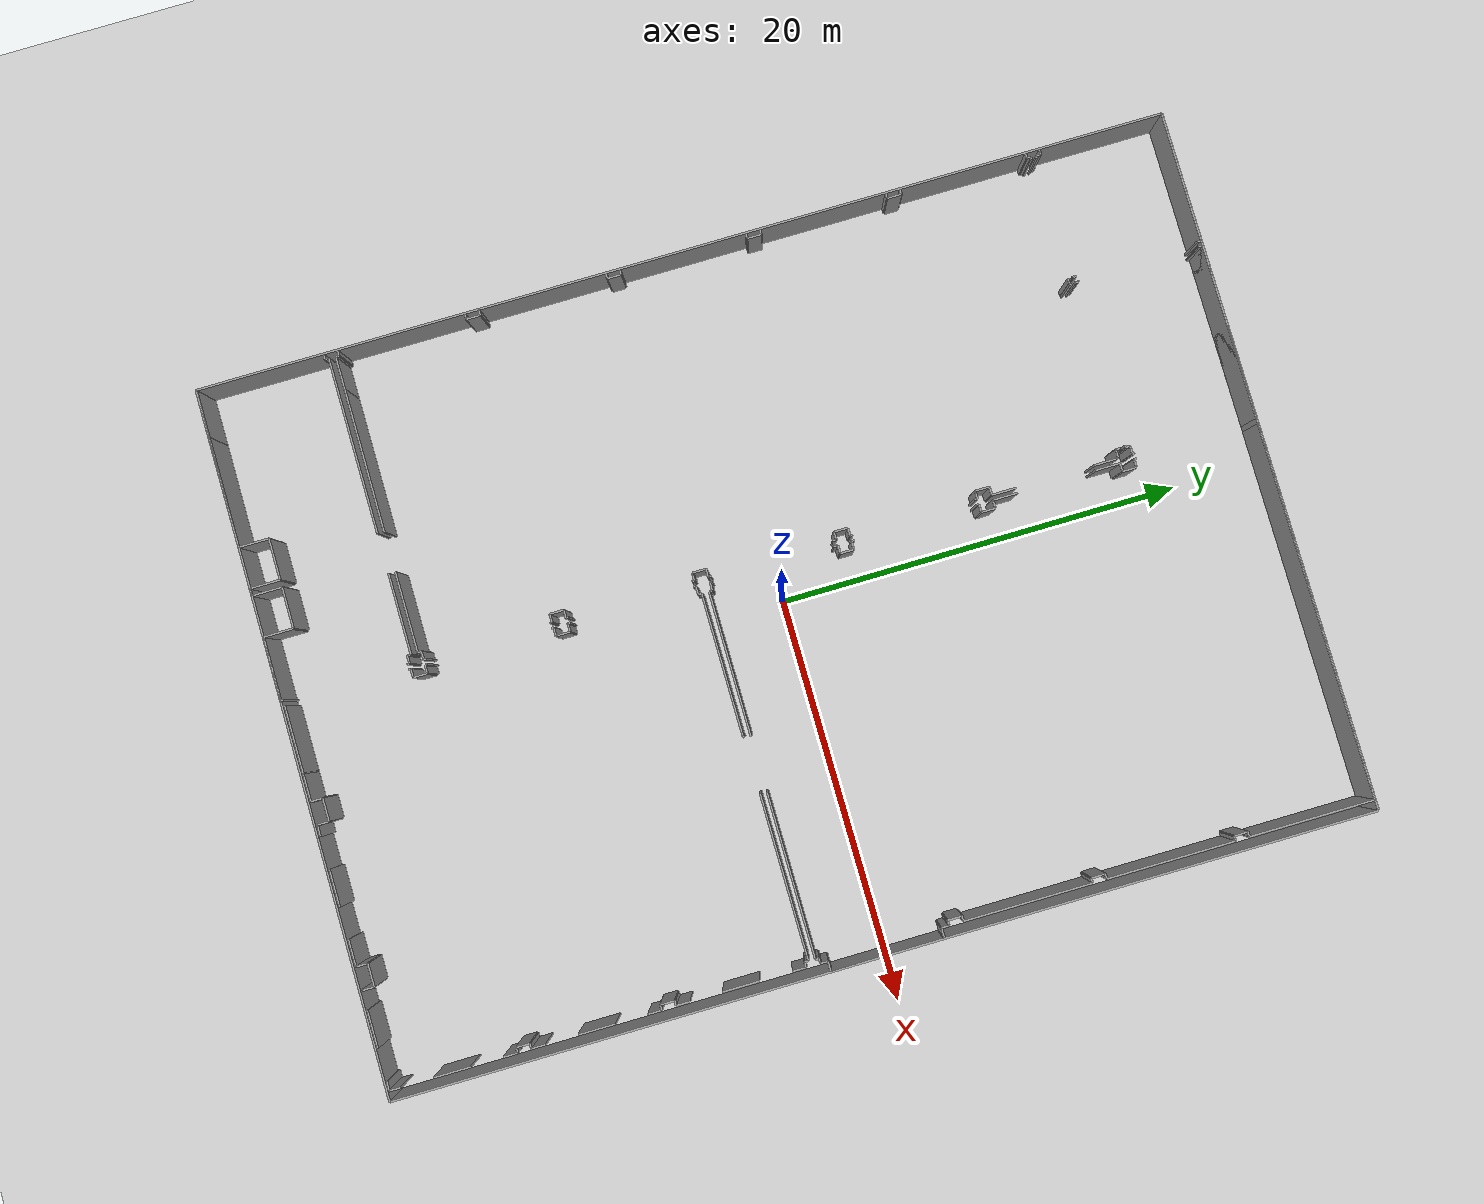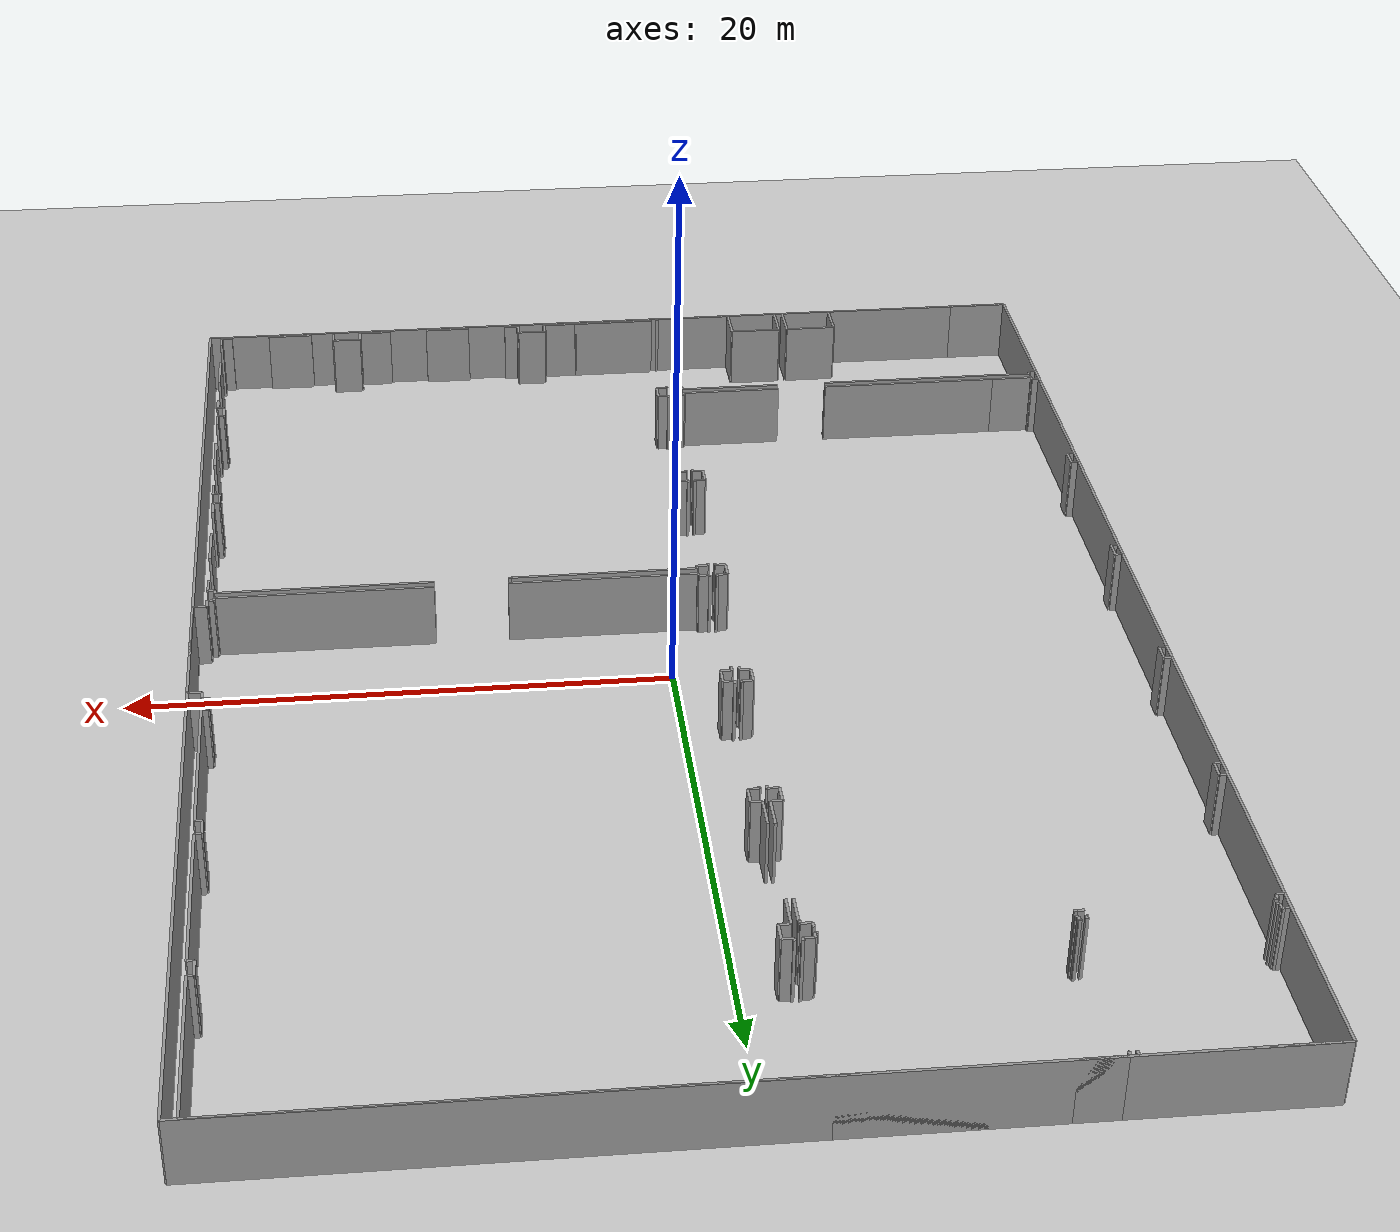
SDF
<sdf version="1.6">
  <world name="default">
    <light name="sun" type="directional">
      <cast_shadows>1</cast_shadows>
      <pose frame="">0 0 10 0 -0 0</pose>
      <diffuse>0.8 0.8 0.8 1</diffuse>
      <specular>0.1 0.1 0.1 1</specular>
      <attenuation>
        <range>1000</range>
        <constant>0.9</constant>
        <linear>0.01</linear>
        <quadratic>0.001</quadratic>
      </attenuation>
      <direction>-0.5 0.5 -1</direction>
    </light>
    <model name="ground_plane">
      <static>1</static>
      <link name="link">
        <collision name="collision">
          <geometry>
            <plane>
              <normal>0 0 1</normal>
              <size>100 100</size>
            </plane>
          </geometry>
          <surface>
            <friction>
              <ode>
                <mu>100</mu>
                <mu2>50</mu2>
              </ode>
              <torsional>
                <ode />
              </torsional>
            </friction>
            <contact>
              <ode />
            </contact>
            <bounce />
          </surface>
          <max_contacts>10</max_contacts>
        </collision>
        <visual name="visual">
          <cast_shadows>0</cast_shadows>
          <geometry>
            <plane>
              <normal>0 0 1</normal>
              <size>100 100</size>
            </plane>
          </geometry>
          <material>
            <script>
              <uri>file://media/materials/scripts/gazebo.material</uri>
              <name>Gazebo/Grey</name>
            </script>
          </material>
        </visual>
        <self_collide>0</self_collide>
        <kinematic>0</kinematic>
        <gravity>1</gravity>
      </link>
    </model>
    <gravity>0 0 -9.8</gravity>
    <magnetic_field>6e-06 2.3e-05 -4.2e-05</magnetic_field>
    <atmosphere type="adiabatic" />
    <physics default="0" name="default_physics" type="ode">
      <max_step_size>0.001</max_step_size>
      <real_time_factor>1</real_time_factor>
      <real_time_update_rate>1000</real_time_update_rate>
    </physics>
    <scene>
      <ambient>0.4 0.4 0.4 1</ambient>
      <background>0.7 0.7 0.7 1</background>
      <shadows>1</shadows>
    </scene>
    <spherical_coordinates>
      <surface_model>EARTH_WGS84</surface_model>
      <latitude_deg>0</latitude_deg>
      <longitude_deg>0</longitude_deg>
      <elevation>0</elevation>
      <heading_deg>0</heading_deg>
    </spherical_coordinates>
  <model name="50055649">
		<static>1</static>
		<link name="Wall_0">
			<collision name="Wall_0_Collision">
				<geometry>
					<box>
						<size>0.191259261142 0.1 2.5</size>
					</box>
				</geometry>
				<pose frame="">0.095629630571 0 1.25 0 0 0</pose>
			</collision>
			<visual name="Wall_0_Visual">
				<pose frame="">0.095629630571 0 1.25 0 0 0</pose>
				<geometry>
					<box>
						<size>0.191259261142 0.1 2.5</size>
					</box>
				</geometry>
				<material>
					<script>
						<uri>file://media/materials/scripts/gazebo.material</uri>
						<name>Gazebo/Grey</name>
					</script>
					<ambient>1 1 1 1</ambient>
				</material>
			</visual>
			<pose frame="">0.208161242359 -6.18383763931 0 0 0 3.14159265359</pose>
		</link>
		<link name="Wall_1">
			<collision name="Wall_1_Collision">
				<geometry>
					<box>
						<size>6.4601151368 0.1 2.5</size>
					</box>
				</geometry>
				<pose frame="">3.2300575684 0 1.25 0 0 0</pose>
			</collision>
			<visual name="Wall_1_Visual">
				<pose frame="">3.2300575684 0 1.25 0 0 0</pose>
				<geometry>
					<box>
						<size>6.4601151368 0.1 2.5</size>
					</box>
				</geometry>
				<material>
					<script>
						<uri>file://media/materials/scripts/gazebo.material</uri>
						<name>Gazebo/Grey</name>
					</script>
					<ambient>1 1 1 1</ambient>
				</material>
			</visual>
			<pose frame="">0.0169019812172 -0.00482913749063 0 0 0 0.0</pose>
		</link>
		<link name="Wall_2">
			<collision name="Wall_2_Collision">
				<geometry>
					<box>
						<size>0.210575811104 0.1 2.5</size>
					</box>
				</geometry>
				<pose frame="">0.105287905552 0 1.25 0 0 0</pose>
			</collision>
			<visual name="Wall_2_Visual">
				<pose frame="">0.105287905552 0 1.25 0 0 0</pose>
				<geometry>
					<box>
						<size>0.210575811104 0.1 2.5</size>
					</box>
				</geometry>
				<material>
					<script>
						<uri>file://media/materials/scripts/gazebo.material</uri>
						<name>Gazebo/Grey</name>
					</script>
					<ambient>1 1 1 1</ambient>
				</material>
			</visual>
			<pose frame="">6.47701711802 -0.00482913749063 0 0 0 -1.57079632679</pose>
		</link>
		<link name="Wall_3">
			<collision name="Wall_3_Collision">
				<geometry>
					<box>
						<size>0.152880326348 0.1 2.5</size>
					</box>
				</geometry>
				<pose frame="">0.076440163174 0 1.25 0 0 0</pose>
			</collision>
			<visual name="Wall_3_Visual">
				<pose frame="">0.076440163174 0 1.25 0 0 0</pose>
				<geometry>
					<box>
						<size>0.152880326348 0.1 2.5</size>
					</box>
				</geometry>
				<material>
					<script>
						<uri>file://media/materials/scripts/gazebo.material</uri>
						<name>Gazebo/Grey</name>
					</script>
					<ambient>1 1 1 1</ambient>
				</material>
			</visual>
			<pose frame="">6.47701711802 -6.26313716021 0 0 0 -1.57079632679</pose>
		</link>
		<link name="Wall_4">
			<collision name="Wall_4_Collision">
				<geometry>
					<box>
						<size>0.0682433376965 0.1 2.5</size>
					</box>
				</geometry>
				<pose frame="">0.0341216688483 0 1.25 0 0 0</pose>
			</collision>
			<visual name="Wall_4_Visual">
				<pose frame="">0.0341216688483 0 1.25 0 0 0</pose>
				<geometry>
					<box>
						<size>0.0682433376965 0.1 2.5</size>
					</box>
				</geometry>
				<material>
					<script>
						<uri>file://media/materials/scripts/gazebo.material</uri>
						<name>Gazebo/Grey</name>
					</script>
					<ambient>1 1 1 1</ambient>
				</material>
			</visual>
			<pose frame="">6.47701711802 -6.41601748656 0 0 0 3.14159265359</pose>
		</link>
		<link name="Wall_5">
			<collision name="Wall_5_Collision">
				<geometry>
					<box>
						<size>0.11462847412 0.1 2.5</size>
					</box>
				</geometry>
				<pose frame="">0.0573142370598 0 1.25 0 0 0</pose>
			</collision>
			<visual name="Wall_5_Visual">
				<pose frame="">0.0573142370598 0 1.25 0 0 0</pose>
				<geometry>
					<box>
						<size>0.11462847412 0.1 2.5</size>
					</box>
				</geometry>
				<material>
					<script>
						<uri>file://media/materials/scripts/gazebo.material</uri>
						<name>Gazebo/Grey</name>
					</script>
					<ambient>1 1 1 1</ambient>
				</material>
			</visual>
			<pose frame="">0.415687071891 -6.41601748656 0 0 0 3.14159265359</pose>
		</link>
		<link name="Wall_6">
			<collision name="Wall_6_Collision">
				<geometry>
					<box>
						<size>0.232179847247 0.1 2.5</size>
					</box>
				</geometry>
				<pose frame="">0.116089923623 0 1.25 0 0 0</pose>
			</collision>
			<visual name="Wall_6_Visual">
				<pose frame="">0.116089923623 0 1.25 0 0 0</pose>
				<geometry>
					<box>
						<size>0.232179847247 0.1 2.5</size>
					</box>
				</geometry>
				<material>
					<script>
						<uri>file://media/materials/scripts/gazebo.material</uri>
						<name>Gazebo/Grey</name>
					</script>
					<ambient>1 1 1 1</ambient>
				</material>
			</visual>
			<pose frame="">0.301058597771 -6.41601748656 0 0 0 1.57079632679</pose>
		</link>
		<link name="Wall_7">
			<collision name="Wall_7_Collision">
				<geometry>
					<box>
						<size>0.0928973554118 0.1 2.5</size>
					</box>
				</geometry>
				<pose frame="">0.0464486777059 0 1.25 0 0 0</pose>
			</collision>
			<visual name="Wall_7_Visual">
				<pose frame="">0.0464486777059 0 1.25 0 0 0</pose>
				<geometry>
					<box>
						<size>0.0928973554118 0.1 2.5</size>
					</box>
				</geometry>
				<material>
					<script>
						<uri>file://media/materials/scripts/gazebo.material</uri>
						<name>Gazebo/Grey</name>
					</script>
					<ambient>1 1 1 1</ambient>
				</material>
			</visual>
			<pose frame="">0.301058597771 -6.18383763931 0 0 0 3.14159265359</pose>
		</link>
		<link name="Wall_8">
			<collision name="Wall_8_Collision">
				<geometry>
					<box>
						<size>1.50974087865 0.1 2.5</size>
					</box>
				</geometry>
				<pose frame="">0.754870439324 0 1.25 0 0 0</pose>
			</collision>
			<visual name="Wall_8_Visual">
				<pose frame="">0.754870439324 0 1.25 0 0 0</pose>
				<geometry>
					<box>
						<size>1.50974087865 0.1 2.5</size>
					</box>
				</geometry>
				<material>
					<script>
						<uri>file://media/materials/scripts/gazebo.material</uri>
						<name>Gazebo/Grey</name>
					</script>
					<ambient>1 1 1 1</ambient>
				</material>
			</visual>
			<pose frame="">6.74147593692 -0.0 0 0 0 0.0</pose>
		</link>
		<link name="Wall_9">
			<collision name="Wall_9_Collision">
				<geometry>
					<box>
						<size>4.66011767846 0.1 2.5</size>
					</box>
				</geometry>
				<pose frame="">2.33005883923 0 1.25 0 0 0</pose>
			</collision>
			<visual name="Wall_9_Visual">
				<pose frame="">2.33005883923 0 1.25 0 0 0</pose>
				<geometry>
					<box>
						<size>4.66011767846 0.1 2.5</size>
					</box>
				</geometry>
				<material>
					<script>
						<uri>file://media/materials/scripts/gazebo.material</uri>
						<name>Gazebo/Grey</name>
					</script>
					<ambient>1 1 1 1</ambient>
				</material>
			</visual>
			<pose frame="">10.7764744755 -0.0 0 0 0 0.0</pose>
		</link>
		<link name="Wall_10">
			<collision name="Wall_10_Collision">
				<geometry>
					<box>
						<size>0.112976400768 0.1 2.5</size>
					</box>
				</geometry>
				<pose frame="">0.0564882003838 0 1.25 0 0 0</pose>
			</collision>
			<visual name="Wall_10_Visual">
				<pose frame="">0.0564882003838 0 1.25 0 0 0</pose>
				<geometry>
					<box>
						<size>0.112976400768 0.1 2.5</size>
					</box>
				</geometry>
				<material>
					<script>
						<uri>file://media/materials/scripts/gazebo.material</uri>
						<name>Gazebo/Grey</name>
					</script>
					<ambient>1 1 1 1</ambient>
				</material>
			</visual>
			<pose frame="">15.4365921539 -6.06565085336 0 0 0 -1.57079632679</pose>
		</link>
		<link name="Wall_11">
			<collision name="Wall_11_Collision">
				<geometry>
					<box>
						<size>0.401199659419 0.1 2.5</size>
					</box>
				</geometry>
				<pose frame="">0.200599829709 0 1.25 0 0 0</pose>
			</collision>
			<visual name="Wall_11_Visual">
				<pose frame="">0.200599829709 0 1.25 0 0 0</pose>
				<geometry>
					<box>
						<size>0.401199659419 0.1 2.5</size>
					</box>
				</geometry>
				<material>
					<script>
						<uri>file://media/materials/scripts/gazebo.material</uri>
						<name>Gazebo/Grey</name>
					</script>
					<ambient>1 1 1 1</ambient>
				</material>
			</visual>
			<pose frame="">15.4365921539 -6.17862725413 0 0 0 3.14159265359</pose>
		</link>
		<link name="Wall_12">
			<collision name="Wall_12_Collision">
				<geometry>
					<box>
						<size>0.226206966666 0.1 2.5</size>
					</box>
				</geometry>
				<pose frame="">0.113103483333 0 1.25 0 0 0</pose>
			</collision>
			<visual name="Wall_12_Visual">
				<pose frame="">0.113103483333 0 1.25 0 0 0</pose>
				<geometry>
					<box>
						<size>0.226206966666 0.1 2.5</size>
					</box>
				</geometry>
				<material>
					<script>
						<uri>file://media/materials/scripts/gazebo.material</uri>
						<name>Gazebo/Grey</name>
					</script>
					<ambient>1 1 1 1</ambient>
				</material>
			</visual>
			<pose frame="">15.0353924945 -6.17862725413 0 0 0 -1.57079632679</pose>
		</link>
		<link name="Wall_13">
			<collision name="Wall_13_Collision">
				<geometry>
					<box>
						<size>0.115136804382 0.1 2.5</size>
					</box>
				</geometry>
				<pose frame="">0.0575684021909 0 1.25 0 0 0</pose>
			</collision>
			<visual name="Wall_13_Visual">
				<pose frame="">0.0575684021909 0 1.25 0 0 0</pose>
				<geometry>
					<box>
						<size>0.115136804382 0.1 2.5</size>
					</box>
				</geometry>
				<material>
					<script>
						<uri>file://media/materials/scripts/gazebo.material</uri>
						<name>Gazebo/Grey</name>
					</script>
					<ambient>1 1 1 1</ambient>
				</material>
			</visual>
			<pose frame="">15.0353924945 -6.40483422079 0 0 0 3.14159265359</pose>
		</link>
		<link name="Wall_14">
			<collision name="Wall_14_Collision">
				<geometry>
					<box>
						<size>0.0974723277714 0.1 2.5</size>
					</box>
				</geometry>
				<pose frame="">0.0487361638857 0 1.25 0 0 0</pose>
			</collision>
			<visual name="Wall_14_Visual">
				<pose frame="">0.0487361638857 0 1.25 0 0 0</pose>
				<geometry>
					<box>
						<size>0.0974723277714 0.1 2.5</size>
					</box>
				</geometry>
				<material>
					<script>
						<uri>file://media/materials/scripts/gazebo.material</uri>
						<name>Gazebo/Grey</name>
					</script>
					<ambient>1 1 1 1</ambient>
				</material>
			</visual>
			<pose frame="">6.84276074165 -6.40483422079 0 0 0 3.14159265359</pose>
		</link>
		<link name="Wall_15">
			<collision name="Wall_15_Collision">
				<geometry>
					<box>
						<size>0.145382454981 0.1 2.5</size>
					</box>
				</geometry>
				<pose frame="">0.0726912274905 0 1.25 0 0 0</pose>
			</collision>
			<visual name="Wall_15_Visual">
				<pose frame="">0.0726912274905 0 1.25 0 0 0</pose>
				<geometry>
					<box>
						<size>0.145382454981 0.1 2.5</size>
					</box>
				</geometry>
				<material>
					<script>
						<uri>file://media/materials/scripts/gazebo.material</uri>
						<name>Gazebo/Grey</name>
					</script>
					<ambient>1 1 1 1</ambient>
				</material>
			</visual>
			<pose frame="">6.74528841388 -6.40483422079 0 0 0 1.57079632679</pose>
		</link>
		<link name="Wall_16">
			<collision name="Wall_16_Collision">
				<geometry>
					<box>
						<size>0.0275769167228 0.1 2.5</size>
					</box>
				</geometry>
				<pose frame="">0.0137884583614 0 1.25 0 0 0</pose>
			</collision>
			<visual name="Wall_16_Visual">
				<pose frame="">0.0137884583614 0 1.25 0 0 0</pose>
				<geometry>
					<box>
						<size>0.0275769167228 0.1 2.5</size>
					</box>
				</geometry>
				<material>
					<script>
						<uri>file://media/materials/scripts/gazebo.material</uri>
						<name>Gazebo/Grey</name>
					</script>
					<ambient>1 1 1 1</ambient>
				</material>
			</visual>
			<pose frame="">6.74528841388 -6.25945176581 0 0 0 3.14159265359</pose>
		</link>
		<link name="Wall_17">
			<collision name="Wall_17_Collision">
				<geometry>
					<box>
						<size>0.0640496130336 0.1 2.5</size>
					</box>
				</geometry>
				<pose frame="">0.0320248065168 0 1.25 0 0 0</pose>
			</collision>
			<visual name="Wall_17_Visual">
				<pose frame="">0.0320248065168 0 1.25 0 0 0</pose>
				<geometry>
					<box>
						<size>0.0640496130336 0.1 2.5</size>
					</box>
				</geometry>
				<material>
					<script>
						<uri>file://media/materials/scripts/gazebo.material</uri>
						<name>Gazebo/Grey</name>
					</script>
					<ambient>1 1 1 1</ambient>
				</material>
			</visual>
			<pose frame="">6.71771149716 -6.25945176581 0 0 0 1.57079632679</pose>
		</link>
		<link name="Wall_18">
			<collision name="Wall_18_Collision">
				<geometry>
					<box>
						<size>0.0062270457116 0.1 2.5</size>
					</box>
				</geometry>
				<pose frame="">0.0031135228558 0 1.25 0 0 0</pose>
			</collision>
			<visual name="Wall_18_Visual">
				<pose frame="">0.0031135228558 0 1.25 0 0 0</pose>
				<geometry>
					<box>
						<size>0.0062270457116 0.1 2.5</size>
					</box>
				</geometry>
				<material>
					<script>
						<uri>file://media/materials/scripts/gazebo.material</uri>
						<name>Gazebo/Grey</name>
					</script>
					<ambient>1 1 1 1</ambient>
				</material>
			</visual>
			<pose frame="">6.71771149716 -0.202061279213 0 0 0 0.0</pose>
		</link>
		<link name="Wall_19">
			<collision name="Wall_19_Collision">
				<geometry>
					<box>
						<size>0.202820908062 0.1 2.5</size>
					</box>
				</geometry>
				<pose frame="">0.101410454031 0 1.25 0 0 0</pose>
			</collision>
			<visual name="Wall_19_Visual">
				<pose frame="">0.101410454031 0 1.25 0 0 0</pose>
				<geometry>
					<box>
						<size>0.202820908062 0.1 2.5</size>
					</box>
				</geometry>
				<material>
					<script>
						<uri>file://media/materials/scripts/gazebo.material</uri>
						<name>Gazebo/Grey</name>
					</script>
					<ambient>1 1 1 1</ambient>
				</material>
			</visual>
			<pose frame="">6.72393854287 -0.202061279213 0 0 0 1.48422082805</pose>
		</link>
		<link name="Wall_20">
			<collision name="Wall_20_Collision">
				<geometry>
					<box>
						<size>1.65931705829 0.1 2.5</size>
					</box>
				</geometry>
				<pose frame="">0.829658529146 0 1.25 0 0 0</pose>
			</collision>
			<visual name="Wall_20_Visual">
				<pose frame="">0.829658529146 0 1.25 0 0 0</pose>
				<geometry>
					<box>
						<size>1.65931705829 0.1 2.5</size>
					</box>
				</geometry>
				<material>
					<script>
						<uri>file://media/materials/scripts/gazebo.material</uri>
						<name>Gazebo/Grey</name>
					</script>
					<ambient>1 1 1 1</ambient>
				</material>
			</visual>
			<pose frame="">1.95821525245 -41.3924436707 0 0 0 3.14159265359</pose>
		</link>
		<link name="Wall_21">
			<collision name="Wall_21_Collision">
				<geometry>
					<box>
						<size>0.160124032584 0.1 2.5</size>
					</box>
				</geometry>
				<pose frame="">0.080062016292 0 1.25 0 0 0</pose>
			</collision>
			<visual name="Wall_21_Visual">
				<pose frame="">0.080062016292 0 1.25 0 0 0</pose>
				<geometry>
					<box>
						<size>0.160124032584 0.1 2.5</size>
					</box>
				</geometry>
				<material>
					<script>
						<uri>file://media/materials/scripts/gazebo.material</uri>
						<name>Gazebo/Grey</name>
					</script>
					<ambient>1 1 1 1</ambient>
				</material>
			</visual>
			<pose frame="">0.298898194157 -41.3924436707 0 0 0 1.57079632679</pose>
		</link>
		<link name="Wall_22">
			<collision name="Wall_22_Collision">
				<geometry>
					<box>
						<size>0.282631625767 0.1 2.5</size>
					</box>
				</geometry>
				<pose frame="">0.141315812884 0 1.25 0 0 0</pose>
			</collision>
			<visual name="Wall_22_Visual">
				<pose frame="">0.141315812884 0 1.25 0 0 0</pose>
				<geometry>
					<box>
						<size>0.282631625767 0.1 2.5</size>
					</box>
				</geometry>
				<material>
					<script>
						<uri>file://media/materials/scripts/gazebo.material</uri>
						<name>Gazebo/Grey</name>
					</script>
					<ambient>1 1 1 1</ambient>
				</material>
			</visual>
			<pose frame="">0.298898194157 -41.2323196381 0 0 0 3.14159265359</pose>
		</link>
		<link name="Wall_23">
			<collision name="Wall_23_Collision">
				<geometry>
					<box>
						<size>0.282123295505 0.1 2.5</size>
					</box>
				</geometry>
				<pose frame="">0.141061647753 0 1.25 0 0 0</pose>
			</collision>
			<visual name="Wall_23_Visual">
				<pose frame="">0.141061647753 0 1.25 0 0 0</pose>
				<geometry>
					<box>
						<size>0.282123295505 0.1 2.5</size>
					</box>
				</geometry>
				<material>
					<script>
						<uri>file://media/materials/scripts/gazebo.material</uri>
						<name>Gazebo/Grey</name>
					</script>
					<ambient>1 1 1 1</ambient>
				</material>
			</visual>
			<pose frame="">0.0162665683895 -34.9051328648 0 0 0 0.0</pose>
		</link>
		<link name="Wall_24">
			<collision name="Wall_24_Collision">
				<geometry>
					<box>
						<size>0.690439578594 0.1 2.5</size>
					</box>
				</geometry>
				<pose frame="">0.345219789297 0 1.25 0 0 0</pose>
			</collision>
			<visual name="Wall_24_Visual">
				<pose frame="">0.345219789297 0 1.25 0 0 0</pose>
				<geometry>
					<box>
						<size>0.690439578594 0.1 2.5</size>
					</box>
				</geometry>
				<material>
					<script>
						<uri>file://media/materials/scripts/gazebo.material</uri>
						<name>Gazebo/Grey</name>
					</script>
					<ambient>1 1 1 1</ambient>
				</material>
			</visual>
			<pose frame="">0.298389863895 -34.9051328648 0 0 0 1.57079632679</pose>
		</link>
		<link name="Wall_25">
			<collision name="Wall_25_Collision">
				<geometry>
					<box>
						<size>0.281487882677 0.1 2.5</size>
					</box>
				</geometry>
				<pose frame="">0.140743941339 0 1.25 0 0 0</pose>
			</collision>
			<visual name="Wall_25_Visual">
				<pose frame="">0.140743941339 0 1.25 0 0 0</pose>
				<geometry>
					<box>
						<size>0.281487882677 0.1 2.5</size>
					</box>
				</geometry>
				<material>
					<script>
						<uri>file://media/materials/scripts/gazebo.material</uri>
						<name>Gazebo/Grey</name>
					</script>
					<ambient>1 1 1 1</ambient>
				</material>
			</visual>
			<pose frame="">0.298389863895 -34.2146932862 0 0 0 3.14159265359</pose>
		</link>
		<link name="Wall_26">
			<collision name="Wall_26_Collision">
				<geometry>
					<box>
						<size>0.267000470206 0.1 2.5</size>
					</box>
				</geometry>
				<pose frame="">0.133500235103 0 1.25 0 0 0</pose>
			</collision>
			<visual name="Wall_26_Visual">
				<pose frame="">0.133500235103 0 1.25 0 0 0</pose>
				<geometry>
					<box>
						<size>0.267000470206 0.1 2.5</size>
					</box>
				</geometry>
				<material>
					<script>
						<uri>file://media/materials/scripts/gazebo.material</uri>
						<name>Gazebo/Grey</name>
					</script>
					<ambient>1 1 1 1</ambient>
				</material>
			</visual>
			<pose frame="">0.0169019812172 -27.8824232104 0 0 0 0.0</pose>
		</link>
		<link name="Wall_27">
			<collision name="Wall_27_Collision">
				<geometry>
					<box>
						<size>0.679129230261 0.1 2.5</size>
					</box>
				</geometry>
				<pose frame="">0.33956461513 0 1.25 0 0 0</pose>
			</collision>
			<visual name="Wall_27_Visual">
				<pose frame="">0.33956461513 0 1.25 0 0 0</pose>
				<geometry>
					<box>
						<size>0.679129230261 0.1 2.5</size>
					</box>
				</geometry>
				<material>
					<script>
						<uri>file://media/materials/scripts/gazebo.material</uri>
						<name>Gazebo/Grey</name>
					</script>
					<ambient>1 1 1 1</ambient>
				</material>
			</visual>
			<pose frame="">0.283902451423 -27.8824232104 0 0 0 1.57079632679</pose>
		</link>
		<link name="Wall_28">
			<collision name="Wall_28_Collision">
				<geometry>
					<box>
						<size>0.263696323501 0.1 2.5</size>
					</box>
				</geometry>
				<pose frame="">0.131848161751 0 1.25 0 0 0</pose>
			</collision>
			<visual name="Wall_28_Visual">
				<pose frame="">0.131848161751 0 1.25 0 0 0</pose>
				<geometry>
					<box>
						<size>0.263696323501 0.1 2.5</size>
					</box>
				</geometry>
				<material>
					<script>
						<uri>file://media/materials/scripts/gazebo.material</uri>
						<name>Gazebo/Grey</name>
					</script>
					<ambient>1 1 1 1</ambient>
				</material>
			</visual>
			<pose frame="">0.283902451423 -27.2032939801 0 0 0 3.14159265359</pose>
		</link>
		<link name="Wall_29">
			<collision name="Wall_29_Collision">
				<geometry>
					<box>
						<size>0.267762965599 0.1 2.5</size>
					</box>
				</geometry>
				<pose frame="">0.133881482799 0 1.25 0 0 0</pose>
			</collision>
			<visual name="Wall_29_Visual">
				<pose frame="">0.133881482799 0 1.25 0 0 0</pose>
				<geometry>
					<box>
						<size>0.267762965599 0.1 2.5</size>
					</box>
				</geometry>
				<material>
					<script>
						<uri>file://media/materials/scripts/gazebo.material</uri>
						<name>Gazebo/Grey</name>
					</script>
					<ambient>1 1 1 1</ambient>
				</material>
			</visual>
			<pose frame="">0.0202061279213 -20.8951695917 0 0 0 0.0</pose>
		</link>
		<link name="Wall_30">
			<collision name="Wall_30_Collision">
				<geometry>
					<box>
						<size>0.689804165766 0.1 2.5</size>
					</box>
				</geometry>
				<pose frame="">0.344902082883 0 1.25 0 0 0</pose>
			</collision>
			<visual name="Wall_30_Visual">
				<pose frame="">0.344902082883 0 1.25 0 0 0</pose>
				<geometry>
					<box>
						<size>0.689804165766 0.1 2.5</size>
					</box>
				</geometry>
				<material>
					<script>
						<uri>file://media/materials/scripts/gazebo.material</uri>
						<name>Gazebo/Grey</name>
					</script>
					<ambient>1 1 1 1</ambient>
				</material>
			</visual>
			<pose frame="">0.28796909352 -20.8951695917 0 0 0 1.57079632679</pose>
		</link>
		<link name="Wall_31">
			<collision name="Wall_31_Collision">
				<geometry>
					<box>
						<size>0.266365057378 0.1 2.5</size>
					</box>
				</geometry>
				<pose frame="">0.133182528689 0 1.25 0 0 0</pose>
			</collision>
			<visual name="Wall_31_Visual">
				<pose frame="">0.133182528689 0 1.25 0 0 0</pose>
				<geometry>
					<box>
						<size>0.266365057378 0.1 2.5</size>
					</box>
				</geometry>
				<material>
					<script>
						<uri>file://media/materials/scripts/gazebo.material</uri>
						<name>Gazebo/Grey</name>
					</script>
					<ambient>1 1 1 1</ambient>
				</material>
			</visual>
			<pose frame="">0.28796909352 -20.2053654259 0 0 0 3.14159265359</pose>
		</link>
		<link name="Wall_32">
			<collision name="Wall_32_Collision">
				<geometry>
					<box>
						<size>0.263060910674 0.1 2.5</size>
					</box>
				</geometry>
				<pose frame="">0.131530455337 0 1.25 0 0 0</pose>
			</collision>
			<visual name="Wall_32_Visual">
				<pose frame="">0.131530455337 0 1.25 0 0 0</pose>
				<geometry>
					<box>
						<size>0.263060910674 0.1 2.5</size>
					</box>
				</geometry>
				<material>
					<script>
						<uri>file://media/materials/scripts/gazebo.material</uri>
						<name>Gazebo/Grey</name>
					</script>
					<ambient>1 1 1 1</ambient>
				</material>
			</visual>
			<pose frame="">0.0216040361423 -13.8977493678 0 0 0 0.0</pose>
		</link>
		<link name="Wall_33">
			<collision name="Wall_33_Collision">
				<geometry>
					<box>
						<size>0.710137376253 0.1 2.5</size>
					</box>
				</geometry>
				<pose frame="">0.355068688127 0 1.25 0 0 0</pose>
			</collision>
			<visual name="Wall_33_Visual">
				<pose frame="">0.355068688127 0 1.25 0 0 0</pose>
				<geometry>
					<box>
						<size>0.710137376253 0.1 2.5</size>
					</box>
				</geometry>
				<material>
					<script>
						<uri>file://media/materials/scripts/gazebo.material</uri>
						<name>Gazebo/Grey</name>
					</script>
					<ambient>1 1 1 1</ambient>
				</material>
			</visual>
			<pose frame="">0.284664946816 -13.8977493678 0 0 0 1.57079632679</pose>
		</link>
		<link name="Wall_34">
			<collision name="Wall_34_Collision">
				<geometry>
					<box>
						<size>0.270812947172 0.1 2.5</size>
					</box>
				</geometry>
				<pose frame="">0.135406473586 0 1.25 0 0 0</pose>
			</collision>
			<visual name="Wall_34_Visual">
				<pose frame="">0.135406473586 0 1.25 0 0 0</pose>
				<geometry>
					<box>
						<size>0.270812947172 0.1 2.5</size>
					</box>
				</geometry>
				<material>
					<script>
						<uri>file://media/materials/scripts/gazebo.material</uri>
						<name>Gazebo/Grey</name>
					</script>
					<ambient>1 1 1 1</ambient>
				</material>
			</visual>
			<pose frame="">0.284664946816 -13.1876119915 0 0 0 3.14159265359</pose>
		</link>
		<link name="Wall_35">
			<collision name="Wall_35_Collision">
				<geometry>
					<box>
						<size>0.270177534344 0.1 2.5</size>
					</box>
				</geometry>
				<pose frame="">0.135088767172 0 1.25 0 0 0</pose>
			</collision>
			<visual name="Wall_35_Visual">
				<pose frame="">0.135088767172 0 1.25 0 0 0</pose>
				<geometry>
					<box>
						<size>0.270177534344 0.1 2.5</size>
					</box>
				</geometry>
				<material>
					<script>
						<uri>file://media/materials/scripts/gazebo.material</uri>
						<name>Gazebo/Grey</name>
					</script>
					<ambient>1 1 1 1</ambient>
				</material>
			</visual>
			<pose frame="">0.0138519996442 -6.8791063554 0 0 0 0.0</pose>
		</link>
		<link name="Wall_36">
			<collision name="Wall_36_Collision">
				<geometry>
					<box>
						<size>0.197613389419 0.1 2.5</size>
					</box>
				</geometry>
				<pose frame="">0.0988066947096 0 1.25 0 0 0</pose>
			</collision>
			<visual name="Wall_36_Visual">
				<pose frame="">0.0988066947096 0 1.25 0 0 0</pose>
				<geometry>
					<box>
						<size>0.197613389419 0.1 2.5</size>
					</box>
				</geometry>
				<material>
					<script>
						<uri>file://media/materials/scripts/gazebo.material</uri>
						<name>Gazebo/Grey</name>
					</script>
					<ambient>1 1 1 1</ambient>
				</material>
			</visual>
			<pose frame="">0.284029533988 -6.8791063554 0 0 0 1.57079632679</pose>
		</link>
		<link name="Wall_37">
			<collision name="Wall_37_Collision">
				<geometry>
					<box>
						<size>0.129370051723 0.1 2.5</size>
					</box>
				</geometry>
				<pose frame="">0.0646850258613 0 1.25 0 0 0</pose>
			</collision>
			<visual name="Wall_37_Visual">
				<pose frame="">0.0646850258613 0 1.25 0 0 0</pose>
				<geometry>
					<box>
						<size>0.129370051723 0.1 2.5</size>
					</box>
				</geometry>
				<material>
					<script>
						<uri>file://media/materials/scripts/gazebo.material</uri>
						<name>Gazebo/Grey</name>
					</script>
					<ambient>1 1 1 1</ambient>
				</material>
			</visual>
			<pose frame="">0.284029533988 -6.68149296598 0 0 0 0.0</pose>
		</link>
		<link name="Wall_38">
			<collision name="Wall_38_Collision">
				<geometry>
					<box>
						<size>0.239042305786 0.1 2.5</size>
					</box>
				</geometry>
				<pose frame="">0.119521152893 0 1.25 0 0 0</pose>
			</collision>
			<visual name="Wall_38_Visual">
				<pose frame="">0.119521152893 0 1.25 0 0 0</pose>
				<geometry>
					<box>
						<size>0.239042305786 0.1 2.5</size>
					</box>
				</geometry>
				<material>
					<script>
						<uri>file://media/materials/scripts/gazebo.material</uri>
						<name>Gazebo/Grey</name>
					</script>
					<ambient>1 1 1 1</ambient>
				</material>
			</visual>
			<pose frame="">6.47091715488 -6.68149296598 0 0 0 0.0</pose>
		</link>
		<link name="Wall_39">
			<collision name="Wall_39_Collision">
				<geometry>
					<box>
						<size>0.0212227884457 0.1 2.5</size>
					</box>
				</geometry>
				<pose frame="">0.0106113942228 0 1.25 0 0 0</pose>
			</collision>
			<visual name="Wall_39_Visual">
				<pose frame="">0.0106113942228 0 1.25 0 0 0</pose>
				<geometry>
					<box>
						<size>0.0212227884457 0.1 2.5</size>
					</box>
				</geometry>
				<material>
					<script>
						<uri>file://media/materials/scripts/gazebo.material</uri>
						<name>Gazebo/Grey</name>
					</script>
					<ambient>1 1 1 1</ambient>
				</material>
			</visual>
			<pose frame="">6.70995946066 -6.68149296598 0 0 0 1.57079632679</pose>
		</link>
		<link name="Wall_40">
			<collision name="Wall_40_Collision">
				<geometry>
					<box>
						<size>0.109291006367 0.1 2.5</size>
					</box>
				</geometry>
				<pose frame="">0.0546455031834 0 1.25 0 0 0</pose>
			</collision>
			<visual name="Wall_40_Visual">
				<pose frame="">0.0546455031834 0 1.25 0 0 0</pose>
				<geometry>
					<box>
						<size>0.109291006367 0.1 2.5</size>
					</box>
				</geometry>
				<material>
					<script>
						<uri>file://media/materials/scripts/gazebo.material</uri>
						<name>Gazebo/Grey</name>
					</script>
					<ambient>1 1 1 1</ambient>
				</material>
			</visual>
			<pose frame="">6.70995946066 -6.66027017753 0 0 0 0.0</pose>
		</link>
		<link name="Wall_41">
			<collision name="Wall_41_Collision">
				<geometry>
					<box>
						<size>0.215150783464 0.1 2.5</size>
					</box>
				</geometry>
				<pose frame="">0.107575391732 0 1.25 0 0 0</pose>
			</collision>
			<visual name="Wall_41_Visual">
				<pose frame="">0.107575391732 0 1.25 0 0 0</pose>
				<geometry>
					<box>
						<size>0.215150783464 0.1 2.5</size>
					</box>
				</geometry>
				<material>
					<script>
						<uri>file://media/materials/scripts/gazebo.material</uri>
						<name>Gazebo/Grey</name>
					</script>
					<ambient>1 1 1 1</ambient>
				</material>
			</visual>
			<pose frame="">15.0116280547 -6.66027017753 0 0 0 -1.57079632679</pose>
		</link>
		<link name="Wall_42">
			<collision name="Wall_42_Collision">
				<geometry>
					<box>
						<size>0.405901714344 0.1 2.5</size>
					</box>
				</geometry>
				<pose frame="">0.202950857172 0 1.25 0 0 0</pose>
			</collision>
			<visual name="Wall_42_Visual">
				<pose frame="">0.202950857172 0 1.25 0 0 0</pose>
				<geometry>
					<box>
						<size>0.405901714344 0.1 2.5</size>
					</box>
				</geometry>
				<material>
					<script>
						<uri>file://media/materials/scripts/gazebo.material</uri>
						<name>Gazebo/Grey</name>
					</script>
					<ambient>1 1 1 1</ambient>
				</material>
			</visual>
			<pose frame="">15.0116280547 -6.875420961 0 0 0 0.0</pose>
		</link>
		<link name="Wall_43">
			<collision name="Wall_43_Collision">
				<geometry>
					<box>
						<size>0.13114920764 0.1 2.5</size>
					</box>
				</geometry>
				<pose frame="">0.0655746038201 0 1.25 0 0 0</pose>
			</collision>
			<visual name="Wall_43_Visual">
				<pose frame="">0.0655746038201 0 1.25 0 0 0</pose>
				<geometry>
					<box>
						<size>0.13114920764 0.1 2.5</size>
					</box>
				</geometry>
				<material>
					<script>
						<uri>file://media/materials/scripts/gazebo.material</uri>
						<name>Gazebo/Grey</name>
					</script>
					<ambient>1 1 1 1</ambient>
				</material>
			</visual>
			<pose frame="">15.4175297691 -6.875420961 0 0 0 -1.57079632679</pose>
		</link>
		<link name="Wall_44">
			<collision name="Wall_44_Collision">
				<geometry>
					<box>
						<size>0.0251623479775 0.1 2.5</size>
					</box>
				</geometry>
				<pose frame="">0.0125811739887 0 1.25 0 0 0</pose>
			</collision>
			<visual name="Wall_44_Visual">
				<pose frame="">0.0125811739887 0 1.25 0 0 0</pose>
				<geometry>
					<box>
						<size>0.0251623479775 0.1 2.5</size>
					</box>
				</geometry>
				<material>
					<script>
						<uri>file://media/materials/scripts/gazebo.material</uri>
						<name>Gazebo/Grey</name>
					</script>
					<ambient>1 1 1 1</ambient>
				</material>
			</visual>
			<pose frame="">15.4175297691 -7.00657016864 0 0 0 0.0</pose>
		</link>
		<link name="Wall_45">
			<collision name="Wall_45_Collision">
				<geometry>
					<box>
						<size>1.0890975867 0.1 2.5</size>
					</box>
				</geometry>
				<pose frame="">0.544548793351 0 1.25 0 0 0</pose>
			</collision>
			<visual name="Wall_45_Visual">
				<pose frame="">0.544548793351 0 1.25 0 0 0</pose>
				<geometry>
					<box>
						<size>1.0890975867 0.1 2.5</size>
					</box>
				</geometry>
				<material>
					<script>
						<uri>file://media/materials/scripts/gazebo.material</uri>
						<name>Gazebo/Grey</name>
					</script>
					<ambient>1 1 1 1</ambient>
				</material>
			</visual>
			<pose frame="">15.4426921171 -7.00657016864 0 0 0 -1.57079632679</pose>
		</link>
		<link name="Wall_46">
			<collision name="Wall_46_Collision">
				<geometry>
					<box>
						<size>1.21757806047 0.1 2.5</size>
					</box>
				</geometry>
				<pose frame="">0.608789030233 0 1.25 0 0 0</pose>
			</collision>
			<visual name="Wall_46_Visual">
				<pose frame="">0.608789030233 0 1.25 0 0 0</pose>
				<geometry>
					<box>
						<size>1.21757806047 0.1 2.5</size>
					</box>
				</geometry>
				<material>
					<script>
						<uri>file://media/materials/scripts/gazebo.material</uri>
						<name>Gazebo/Grey</name>
					</script>
					<ambient>1 1 1 1</ambient>
				</material>
			</visual>
			<pose frame="">15.4426921171 -11.9645693807 0 0 0 -1.57079632679</pose>
		</link>
		<link name="Wall_47">
			<collision name="Wall_47_Collision">
				<geometry>
					<box>
						<size>0.407680870261 0.1 2.5</size>
					</box>
				</geometry>
				<pose frame="">0.203840435131 0 1.25 0 0 0</pose>
			</collision>
			<visual name="Wall_47_Visual">
				<pose frame="">0.203840435131 0 1.25 0 0 0</pose>
				<geometry>
					<box>
						<size>0.407680870261 0.1 2.5</size>
					</box>
				</geometry>
				<material>
					<script>
						<uri>file://media/materials/scripts/gazebo.material</uri>
						<name>Gazebo/Grey</name>
					</script>
					<ambient>1 1 1 1</ambient>
				</material>
			</visual>
			<pose frame="">15.4426921171 -13.1821474412 0 0 0 3.14159265359</pose>
		</link>
		<link name="Wall_48">
			<collision name="Wall_48_Collision">
				<geometry>
					<box>
						<size>0.707468642377 0.1 2.5</size>
					</box>
				</geometry>
				<pose frame="">0.353734321188 0 1.25 0 0 0</pose>
			</collision>
			<visual name="Wall_48_Visual">
				<pose frame="">0.353734321188 0 1.25 0 0 0</pose>
				<geometry>
					<box>
						<size>0.707468642377 0.1 2.5</size>
					</box>
				</geometry>
				<material>
					<script>
						<uri>file://media/materials/scripts/gazebo.material</uri>
						<name>Gazebo/Grey</name>
					</script>
					<ambient>1 1 1 1</ambient>
				</material>
			</visual>
			<pose frame="">15.0350112468 -13.1821474412 0 0 0 -1.57079632679</pose>
		</link>
		<link name="Wall_49">
			<collision name="Wall_49_Collision">
				<geometry>
					<box>
						<size>0.398785090673 0.1 2.5</size>
					</box>
				</geometry>
				<pose frame="">0.199392545337 0 1.25 0 0 0</pose>
			</collision>
			<visual name="Wall_49_Visual">
				<pose frame="">0.199392545337 0 1.25 0 0 0</pose>
				<geometry>
					<box>
						<size>0.398785090673 0.1 2.5</size>
					</box>
				</geometry>
				<material>
					<script>
						<uri>file://media/materials/scripts/gazebo.material</uri>
						<name>Gazebo/Grey</name>
					</script>
					<ambient>1 1 1 1</ambient>
				</material>
			</visual>
			<pose frame="">15.0350112468 -13.8896160836 0 0 0 0.0</pose>
		</link>
		<link name="Wall_50">
			<collision name="Wall_50_Collision">
				<geometry>
					<box>
						<size>0.133817941517 0.1 2.5</size>
					</box>
				</geometry>
				<pose frame="">0.0669089707583 0 1.25 0 0 0</pose>
			</collision>
			<visual name="Wall_50_Visual">
				<pose frame="">0.0669089707583 0 1.25 0 0 0</pose>
				<geometry>
					<box>
						<size>0.133817941517 0.1 2.5</size>
					</box>
				</geometry>
				<material>
					<script>
						<uri>file://media/materials/scripts/gazebo.material</uri>
						<name>Gazebo/Grey</name>
					</script>
					<ambient>1 1 1 1</ambient>
				</material>
			</visual>
			<pose frame="">15.4337963375 -13.8896160836 0 0 0 -1.57079632679</pose>
		</link>
		<link name="Wall_51">
			<collision name="Wall_51_Collision">
				<geometry>
					<box>
						<size>0.128480473764 0.1 2.5</size>
					</box>
				</geometry>
				<pose frame="">0.0642402368819 0 1.25 0 0 0</pose>
			</collision>
			<visual name="Wall_51_Visual">
				<pose frame="">0.0642402368819 0 1.25 0 0 0</pose>
				<geometry>
					<box>
						<size>0.128480473764 0.1 2.5</size>
					</box>
				</geometry>
				<material>
					<script>
						<uri>file://media/materials/scripts/gazebo.material</uri>
						<name>Gazebo/Grey</name>
					</script>
					<ambient>1 1 1 1</ambient>
				</material>
			</visual>
			<pose frame="">15.4337963375 -20.0765037045 0 0 0 -1.57079632679</pose>
		</link>
		<link name="Wall_52">
			<collision name="Wall_52_Collision">
				<geometry>
					<box>
						<size>0.401580907115 0.1 2.5</size>
					</box>
				</geometry>
				<pose frame="">0.200790453558 0 1.25 0 0 0</pose>
			</collision>
			<visual name="Wall_52_Visual">
				<pose frame="">0.200790453558 0 1.25 0 0 0</pose>
				<geometry>
					<box>
						<size>0.401580907115 0.1 2.5</size>
					</box>
				</geometry>
				<material>
					<script>
						<uri>file://media/materials/scripts/gazebo.material</uri>
						<name>Gazebo/Grey</name>
					</script>
					<ambient>1 1 1 1</ambient>
				</material>
			</visual>
			<pose frame="">15.4337963375 -20.2049841782 0 0 0 3.14159265359</pose>
		</link>
		<link name="Wall_53">
			<collision name="Wall_53_Collision">
				<geometry>
					<box>
						<size>0.682814624662 0.1 2.5</size>
					</box>
				</geometry>
				<pose frame="">0.341407312331 0 1.25 0 0 0</pose>
			</collision>
			<visual name="Wall_53_Visual">
				<pose frame="">0.341407312331 0 1.25 0 0 0</pose>
				<geometry>
					<box>
						<size>0.682814624662 0.1 2.5</size>
					</box>
				</geometry>
				<material>
					<script>
						<uri>file://media/materials/scripts/gazebo.material</uri>
						<name>Gazebo/Grey</name>
					</script>
					<ambient>1 1 1 1</ambient>
				</material>
			</visual>
			<pose frame="">15.0322154304 -20.2049841782 0 0 0 -1.57079632679</pose>
		</link>
		<link name="Wall_54">
			<collision name="Wall_54_Collision">
				<geometry>
					<box>
						<size>0.396116356797 0.1 2.5</size>
					</box>
				</geometry>
				<pose frame="">0.198058178399 0 1.25 0 0 0</pose>
			</collision>
			<visual name="Wall_54_Visual">
				<pose frame="">0.198058178399 0 1.25 0 0 0</pose>
				<geometry>
					<box>
						<size>0.396116356797 0.1 2.5</size>
					</box>
				</geometry>
				<material>
					<script>
						<uri>file://media/materials/scripts/gazebo.material</uri>
						<name>Gazebo/Grey</name>
					</script>
					<ambient>1 1 1 1</ambient>
				</material>
			</visual>
			<pose frame="">15.0322154304 -20.8877988029 0 0 0 0.0</pose>
		</link>
		<link name="Wall_55">
			<collision name="Wall_55_Collision">
				<geometry>
					<box>
						<size>0.180330160505 0.1 2.5</size>
					</box>
				</geometry>
				<pose frame="">0.0901650802526 0 1.25 0 0 0</pose>
			</collision>
			<visual name="Wall_55_Visual">
				<pose frame="">0.0901650802526 0 1.25 0 0 0</pose>
				<geometry>
					<box>
						<size>0.180330160505 0.1 2.5</size>
					</box>
				</geometry>
				<material>
					<script>
						<uri>file://media/materials/scripts/gazebo.material</uri>
						<name>Gazebo/Grey</name>
					</script>
					<ambient>1 1 1 1</ambient>
				</material>
			</visual>
			<pose frame="">15.4283317872 -20.8877988029 0 0 0 -1.57079632679</pose>
		</link>
		<link name="Wall_56">
			<collision name="Wall_56_Collision">
				<geometry>
					<box>
						<size>0.140044987228 0.1 2.5</size>
					</box>
				</geometry>
				<pose frame="">0.0700224936141 0 1.25 0 0 0</pose>
			</collision>
			<visual name="Wall_56_Visual">
				<pose frame="">0.0700224936141 0 1.25 0 0 0</pose>
				<geometry>
					<box>
						<size>0.140044987228 0.1 2.5</size>
					</box>
				</geometry>
				<material>
					<script>
						<uri>file://media/materials/scripts/gazebo.material</uri>
						<name>Gazebo/Grey</name>
					</script>
					<ambient>1 1 1 1</ambient>
				</material>
			</visual>
			<pose frame="">15.4283317872 -27.0734155981 0 0 0 -1.57079632679</pose>
		</link>
		<link name="Wall_57">
			<collision name="Wall_57_Collision">
				<geometry>
					<box>
						<size>0.3957351091 0.1 2.5</size>
					</box>
				</geometry>
				<pose frame="">0.19786755455 0 1.25 0 0 0</pose>
			</collision>
			<visual name="Wall_57_Visual">
				<pose frame="">0.19786755455 0 1.25 0 0 0</pose>
				<geometry>
					<box>
						<size>0.3957351091 0.1 2.5</size>
					</box>
				</geometry>
				<material>
					<script>
						<uri>file://media/materials/scripts/gazebo.material</uri>
						<name>Gazebo/Grey</name>
					</script>
					<ambient>1 1 1 1</ambient>
				</material>
			</visual>
			<pose frame="">15.4283317872 -27.2134605853 0 0 0 3.14159265359</pose>
		</link>
		<link name="Wall_58">
			<collision name="Wall_58_Collision">
				<geometry>
					<box>
						<size>0.681797964137 0.1 2.5</size>
					</box>
				</geometry>
				<pose frame="">0.340898982069 0 1.25 0 0 0</pose>
			</collision>
			<visual name="Wall_58_Visual">
				<pose frame="">0.340898982069 0 1.25 0 0 0</pose>
				<geometry>
					<box>
						<size>0.681797964137 0.1 2.5</size>
					</box>
				</geometry>
				<material>
					<script>
						<uri>file://media/materials/scripts/gazebo.material</uri>
						<name>Gazebo/Grey</name>
					</script>
					<ambient>1 1 1 1</ambient>
				</material>
			</visual>
			<pose frame="">15.0325966781 -27.2134605853 0 0 0 -1.57079632679</pose>
		</link>
		<link name="Wall_59">
			<collision name="Wall_59_Collision">
				<geometry>
					<box>
						<size>0.391922632134 0.1 2.5</size>
					</box>
				</geometry>
				<pose frame="">0.195961316067 0 1.25 0 0 0</pose>
			</collision>
			<visual name="Wall_59_Visual">
				<pose frame="">0.195961316067 0 1.25 0 0 0</pose>
				<geometry>
					<box>
						<size>0.391922632134 0.1 2.5</size>
					</box>
				</geometry>
				<material>
					<script>
						<uri>file://media/materials/scripts/gazebo.material</uri>
						<name>Gazebo/Grey</name>
					</script>
					<ambient>1 1 1 1</ambient>
				</material>
			</visual>
			<pose frame="">15.0325966781 -27.8952585495 0 0 0 0.0</pose>
		</link>
		<link name="Wall_60">
			<collision name="Wall_60_Collision">
				<geometry>
					<box>
						<size>0.125811739887 0.1 2.5</size>
					</box>
				</geometry>
				<pose frame="">0.0629058699437 0 1.25 0 0 0</pose>
			</collision>
			<visual name="Wall_60_Visual">
				<pose frame="">0.0629058699437 0 1.25 0 0 0</pose>
				<geometry>
					<box>
						<size>0.125811739887 0.1 2.5</size>
					</box>
				</geometry>
				<material>
					<script>
						<uri>file://media/materials/scripts/gazebo.material</uri>
						<name>Gazebo/Grey</name>
					</script>
					<ambient>1 1 1 1</ambient>
				</material>
			</visual>
			<pose frame="">15.4245193102 -27.8952585495 0 0 0 -1.57079632679</pose>
		</link>
		<link name="Wall_61">
			<collision name="Wall_61_Collision">
				<geometry>
					<box>
						<size>0.12632007015 0.1 2.5</size>
					</box>
				</geometry>
				<pose frame="">0.0631600350748 0 1.25 0 0 0</pose>
			</collision>
			<visual name="Wall_61_Visual">
				<pose frame="">0.0631600350748 0 1.25 0 0 0</pose>
				<geometry>
					<box>
						<size>0.12632007015 0.1 2.5</size>
					</box>
				</geometry>
				<material>
					<script>
						<uri>file://media/materials/scripts/gazebo.material</uri>
						<name>Gazebo/Grey</name>
					</script>
					<ambient>1 1 1 1</ambient>
				</material>
			</visual>
			<pose frame="">15.4245193102 -34.0952356746 0 0 0 -1.57079632679</pose>
		</link>
		<link name="Wall_62">
			<collision name="Wall_62_Collision">
				<geometry>
					<box>
						<size>0.402978815336 0.1 2.5</size>
					</box>
				</geometry>
				<pose frame="">0.201489407668 0 1.25 0 0 0</pose>
			</collision>
			<visual name="Wall_62_Visual">
				<pose frame="">0.201489407668 0 1.25 0 0 0</pose>
				<geometry>
					<box>
						<size>0.402978815336 0.1 2.5</size>
					</box>
				</geometry>
				<material>
					<script>
						<uri>file://media/materials/scripts/gazebo.material</uri>
						<name>Gazebo/Grey</name>
					</script>
					<ambient>1 1 1 1</ambient>
				</material>
			</visual>
			<pose frame="">15.4245193102 -34.2215557448 0 0 0 3.14159265359</pose>
		</link>
		<link name="Wall_63">
			<collision name="Wall_63_Collision">
				<geometry>
					<box>
						<size>0.690058330898 0.1 2.5</size>
					</box>
				</geometry>
				<pose frame="">0.345029165449 0 1.25 0 0 0</pose>
			</collision>
			<visual name="Wall_63_Visual">
				<pose frame="">0.345029165449 0 1.25 0 0 0</pose>
				<geometry>
					<box>
						<size>0.690058330898 0.1 2.5</size>
					</box>
				</geometry>
				<material>
					<script>
						<uri>file://media/materials/scripts/gazebo.material</uri>
						<name>Gazebo/Grey</name>
					</script>
					<ambient>1 1 1 1</ambient>
				</material>
			</visual>
			<pose frame="">15.0215404949 -34.2215557448 0 0 0 -1.57079632679</pose>
		</link>
		<link name="Wall_64">
			<collision name="Wall_64_Collision">
				<geometry>
					<box>
						<size>0.412255842621 0.1 2.5</size>
					</box>
				</geometry>
				<pose frame="">0.20612792131 0 1.25 0 0 0</pose>
			</collision>
			<visual name="Wall_64_Visual">
				<pose frame="">0.20612792131 0 1.25 0 0 0</pose>
				<geometry>
					<box>
						<size>0.412255842621 0.1 2.5</size>
					</box>
				</geometry>
				<material>
					<script>
						<uri>file://media/materials/scripts/gazebo.material</uri>
						<name>Gazebo/Grey</name>
					</script>
					<ambient>1 1 1 1</ambient>
				</material>
			</visual>
			<pose frame="">15.0215404949 -34.9116140757 0 0 0 0.0</pose>
		</link>
		<link name="Wall_65">
			<collision name="Wall_65_Collision">
				<geometry>
					<box>
						<size>0.109291006367 0.1 2.5</size>
					</box>
				</geometry>
				<pose frame="">0.0546455031834 0 1.25 0 0 0</pose>
			</collision>
			<visual name="Wall_65_Visual">
				<pose frame="">0.0546455031834 0 1.25 0 0 0</pose>
				<geometry>
					<box>
						<size>0.109291006367 0.1 2.5</size>
					</box>
				</geometry>
				<material>
					<script>
						<uri>file://media/materials/scripts/gazebo.material</uri>
						<name>Gazebo/Grey</name>
					</script>
					<ambient>1 1 1 1</ambient>
				</material>
			</visual>
			<pose frame="">15.4337963375 -34.9116140757 0 0 0 -1.57079632679</pose>
		</link>
		<link name="Wall_66">
			<collision name="Wall_66_Collision">
				<geometry>
					<box>
						<size>0.116280547472 0.1 2.5</size>
					</box>
				</geometry>
				<pose frame="">0.0581402737358 0 1.25 0 0 0</pose>
			</collision>
			<visual name="Wall_66_Visual">
				<pose frame="">0.0581402737358 0 1.25 0 0 0</pose>
				<geometry>
					<box>
						<size>0.116280547472 0.1 2.5</size>
					</box>
				</geometry>
				<material>
					<script>
						<uri>file://media/materials/scripts/gazebo.material</uri>
						<name>Gazebo/Grey</name>
					</script>
					<ambient>1 1 1 1</ambient>
				</material>
			</visual>
			<pose frame="">15.4337963375 -41.1066349807 0 0 0 -1.57079632679</pose>
		</link>
		<link name="Wall_67">
			<collision name="Wall_67_Collision">
				<geometry>
					<box>
						<size>0.404630888688 0.1 2.5</size>
					</box>
				</geometry>
				<pose frame="">0.202315444344 0 1.25 0 0 0</pose>
			</collision>
			<visual name="Wall_67_Visual">
				<pose frame="">0.202315444344 0 1.25 0 0 0</pose>
				<geometry>
					<box>
						<size>0.404630888688 0.1 2.5</size>
					</box>
				</geometry>
				<material>
					<script>
						<uri>file://media/materials/scripts/gazebo.material</uri>
						<name>Gazebo/Grey</name>
					</script>
					<ambient>1 1 1 1</ambient>
				</material>
			</visual>
			<pose frame="">15.4337963375 -41.2229155282 0 0 0 3.14159265359</pose>
		</link>
		<link name="Wall_68">
			<collision name="Wall_68_Collision">
				<geometry>
					<box>
						<size>0.17905933485 0.1 2.5</size>
					</box>
				</geometry>
				<pose frame="">0.0895296674249 0 1.25 0 0 0</pose>
			</collision>
			<visual name="Wall_68_Visual">
				<pose frame="">0.0895296674249 0 1.25 0 0 0</pose>
				<geometry>
					<box>
						<size>0.17905933485 0.1 2.5</size>
					</box>
				</geometry>
				<material>
					<script>
						<uri>file://media/materials/scripts/gazebo.material</uri>
						<name>Gazebo/Grey</name>
					</script>
					<ambient>1 1 1 1</ambient>
				</material>
			</visual>
			<pose frame="">15.0291654488 -41.2229155282 0 0 0 -1.57079632679</pose>
		</link>
		<link name="Wall_69">
			<collision name="Wall_69_Collision">
				<geometry>
					<box>
						<size>3.988359237 0.1 2.5</size>
					</box>
				</geometry>
				<pose frame="">1.9941796185 0 1.25 0 0 0</pose>
			</collision>
			<visual name="Wall_69_Visual">
				<pose frame="">1.9941796185 0 1.25 0 0 0</pose>
				<geometry>
					<box>
						<size>3.988359237 0.1 2.5</size>
					</box>
				</geometry>
				<material>
					<script>
						<uri>file://media/materials/scripts/gazebo.material</uri>
						<name>Gazebo/Grey</name>
					</script>
					<ambient>1 1 1 1</ambient>
				</material>
			</visual>
			<pose frame="">15.0291654488 -41.4019748631 0 0 0 3.14159265359</pose>
		</link>
		<link name="Wall_70">
			<collision name="Wall_70_Collision">
				<geometry>
					<box>
						<size>7.10989468296 0.1 2.5</size>
					</box>
				</geometry>
				<pose frame="">3.55494734148 0 1.25 0 0 0</pose>
			</collision>
			<visual name="Wall_70_Visual">
				<pose frame="">3.55494734148 0 1.25 0 0 0</pose>
				<geometry>
					<box>
						<size>7.10989468296 0.1 2.5</size>
					</box>
				</geometry>
				<material>
					<script>
						<uri>file://media/materials/scripts/gazebo.material</uri>
						<name>Gazebo/Grey</name>
					</script>
					<ambient>1 1 1 1</ambient>
				</material>
			</visual>
			<pose frame="">9.06810354687 -41.4019748631 0 0 0 3.14025209994</pose>
		</link>
		<link name="Wall_71">
			<collision name="Wall_71_Collision">
				<geometry>
					<box>
						<size>2.38330643419 0.1 2.5</size>
					</box>
				</geometry>
				<pose frame="">1.1916532171 0 1.25 0 0 0</pose>
			</collision>
			<visual name="Wall_71_Visual">
				<pose frame="">1.1916532171 0 1.25 0 0 0</pose>
				<geometry>
					<box>
						<size>2.38330643419 0.1 2.5</size>
					</box>
				</geometry>
				<material>
					<script>
						<uri>file://media/materials/scripts/gazebo.material</uri>
						<name>Gazebo/Grey</name>
					</script>
					<ambient>1 1 1 1</ambient>
				</material>
			</visual>
			<pose frame="">2.38330643419 -48.2114399726 0 0 0 3.14159265359</pose>
		</link>
		<link name="Wall_72">
			<collision name="Wall_72_Collision">
				<geometry>
					<box>
						<size>0.290129497134 0.1 2.5</size>
					</box>
				</geometry>
				<pose frame="">0.145064748567 0 1.25 0 0 0</pose>
			</collision>
			<visual name="Wall_72_Visual">
				<pose frame="">0.145064748567 0 1.25 0 0 0</pose>
				<geometry>
					<box>
						<size>0.290129497134 0.1 2.5</size>
					</box>
				</geometry>
				<material>
					<script>
						<uri>file://media/materials/scripts/gazebo.material</uri>
						<name>Gazebo/Grey</name>
					</script>
					<ambient>1 1 1 1</ambient>
				</material>
			</visual>
			<pose frame="">0.0 -41.9180571617 0 0 0 0.0</pose>
		</link>
		<link name="Wall_73">
			<collision name="Wall_73_Collision">
				<geometry>
					<box>
						<size>0.1884634447 0.1 2.5</size>
					</box>
				</geometry>
				<pose frame="">0.09423172235 0 1.25 0 0 0</pose>
			</collision>
			<visual name="Wall_73_Visual">
				<pose frame="">0.09423172235 0 1.25 0 0 0</pose>
				<geometry>
					<box>
						<size>0.1884634447 0.1 2.5</size>
					</box>
				</geometry>
				<material>
					<script>
						<uri>file://media/materials/scripts/gazebo.material</uri>
						<name>Gazebo/Grey</name>
					</script>
					<ambient>1 1 1 1</ambient>
				</material>
			</visual>
			<pose frame="">0.290129497134 -41.9180571617 0 0 0 1.57079632679</pose>
		</link>
		<link name="Wall_74">
			<collision name="Wall_74_Collision">
				<geometry>
					<box>
						<size>8.75459085768 0.1 2.5</size>
					</box>
				</geometry>
				<pose frame="">4.37729542884 0 1.25 0 0 0</pose>
			</collision>
			<visual name="Wall_74_Visual">
				<pose frame="">4.37729542884 0 1.25 0 0 0</pose>
				<geometry>
					<box>
						<size>8.75459085768 0.1 2.5</size>
					</box>
				</geometry>
				<material>
					<script>
						<uri>file://media/materials/scripts/gazebo.material</uri>
						<name>Gazebo/Grey</name>
					</script>
					<ambient>1 1 1 1</ambient>
				</material>
			</visual>
			<pose frame="">0.290129497134 -41.729593717 0 0 0 0.0</pose>
		</link>
		<link name="Wall_75">
			<collision name="Wall_75_Collision">
				<geometry>
					<box>
						<size>4.00170290638 0.1 2.5</size>
					</box>
				</geometry>
				<pose frame="">2.00085145319 0 1.25 0 0 0</pose>
			</collision>
			<visual name="Wall_75_Visual">
				<pose frame="">2.00085145319 0 1.25 0 0 0</pose>
				<geometry>
					<box>
						<size>4.00170290638 0.1 2.5</size>
					</box>
				</geometry>
				<material>
					<script>
						<uri>file://media/materials/scripts/gazebo.material</uri>
						<name>Gazebo/Grey</name>
					</script>
					<ambient>1 1 1 1</ambient>
				</material>
			</visual>
			<pose frame="">11.0274625424 -41.729593717 0 0 0 0.0</pose>
		</link>
		<link name="Wall_76">
			<collision name="Wall_76_Collision">
				<geometry>
					<box>
						<size>0.181219738464 0.1 2.5</size>
					</box>
				</geometry>
				<pose frame="">0.090609869232 0 1.25 0 0 0</pose>
			</collision>
			<visual name="Wall_76_Visual">
				<pose frame="">0.090609869232 0 1.25 0 0 0</pose>
				<geometry>
					<box>
						<size>0.181219738464 0.1 2.5</size>
					</box>
				</geometry>
				<material>
					<script>
						<uri>file://media/materials/scripts/gazebo.material</uri>
						<name>Gazebo/Grey</name>
					</script>
					<ambient>1 1 1 1</ambient>
				</material>
			</visual>
			<pose frame="">15.0291654488 -41.729593717 0 0 0 -1.57079632679</pose>
		</link>
		<link name="Wall_77">
			<collision name="Wall_77_Collision">
				<geometry>
					<box>
						<size>0.392685127527 0.1 2.5</size>
					</box>
				</geometry>
				<pose frame="">0.196342563764 0 1.25 0 0 0</pose>
			</collision>
			<visual name="Wall_77_Visual">
				<pose frame="">0.196342563764 0 1.25 0 0 0</pose>
				<geometry>
					<box>
						<size>0.392685127527 0.1 2.5</size>
					</box>
				</geometry>
				<material>
					<script>
						<uri>file://media/materials/scripts/gazebo.material</uri>
						<name>Gazebo/Grey</name>
					</script>
					<ambient>1 1 1 1</ambient>
				</material>
			</visual>
			<pose frame="">15.0291654488 -41.9108134555 0 0 0 0.0</pose>
		</link>
		<link name="Wall_78">
			<collision name="Wall_78_Collision">
				<geometry>
					<box>
						<size>0.122507593183 0.1 2.5</size>
					</box>
				</geometry>
				<pose frame="">0.0612537965917 0 1.25 0 0 0</pose>
			</collision>
			<visual name="Wall_78_Visual">
				<pose frame="">0.0612537965917 0 1.25 0 0 0</pose>
				<geometry>
					<box>
						<size>0.122507593183 0.1 2.5</size>
					</box>
				</geometry>
				<material>
					<script>
						<uri>file://media/materials/scripts/gazebo.material</uri>
						<name>Gazebo/Grey</name>
					</script>
					<ambient>1 1 1 1</ambient>
				</material>
			</visual>
			<pose frame="">15.4218505763 -41.9108134555 0 0 0 -1.57079632679</pose>
		</link>
		<link name="Wall_79">
			<collision name="Wall_79_Collision">
				<geometry>
					<box>
						<size>0.118695116217 0.1 2.5</size>
					</box>
				</geometry>
				<pose frame="">0.0593475581085 0 1.25 0 0 0</pose>
			</collision>
			<visual name="Wall_79_Visual">
				<pose frame="">0.0593475581085 0 1.25 0 0 0</pose>
				<geometry>
					<box>
						<size>0.118695116217 0.1 2.5</size>
					</box>
				</geometry>
				<material>
					<script>
						<uri>file://media/materials/scripts/gazebo.material</uri>
						<name>Gazebo/Grey</name>
					</script>
					<ambient>1 1 1 1</ambient>
				</material>
			</visual>
			<pose frame="">15.4218505763 -48.0921094435 0 0 0 -1.57079632679</pose>
		</link>
		<link name="Wall_80">
			<collision name="Wall_80_Collision">
				<geometry>
					<box>
						<size>3.13499980938 0.1 2.5</size>
					</box>
				</geometry>
				<pose frame="">1.56749990469 0 1.25 0 0 0</pose>
			</collision>
			<visual name="Wall_80_Visual">
				<pose frame="">1.56749990469 0 1.25 0 0 0</pose>
				<geometry>
					<box>
						<size>3.13499980938 0.1 2.5</size>
					</box>
				</geometry>
				<material>
					<script>
						<uri>file://media/materials/scripts/gazebo.material</uri>
						<name>Gazebo/Grey</name>
					</script>
					<ambient>1 1 1 1</ambient>
				</material>
			</visual>
			<pose frame="">15.4218505763 -48.2108045597 0 0 0 3.14159265359</pose>
		</link>
		<link name="Wall_81">
			<collision name="Wall_81_Collision">
				<geometry>
					<box>
						<size>1.46615155867 0.1 2.5</size>
					</box>
				</geometry>
				<pose frame="">0.733075779334 0 1.25 0 0 0</pose>
			</collision>
			<visual name="Wall_81_Visual">
				<pose frame="">0.733075779334 0 1.25 0 0 0</pose>
				<geometry>
					<box>
						<size>1.46615155867 0.1 2.5</size>
					</box>
				</geometry>
				<material>
					<script>
						<uri>file://media/materials/scripts/gazebo.material</uri>
						<name>Gazebo/Grey</name>
					</script>
					<ambient>1 1 1 1</ambient>
				</material>
			</visual>
			<pose frame="">12.2868507669 -48.2108045597 0 0 0 1.57079632679</pose>
		</link>
		<link name="Wall_82">
			<collision name="Wall_82_Collision">
				<geometry>
					<box>
						<size>2.04297932367 0.1 2.5</size>
					</box>
				</geometry>
				<pose frame="">1.02148966183 0 1.25 0 0 0</pose>
			</collision>
			<visual name="Wall_82_Visual">
				<pose frame="">1.02148966183 0 1.25 0 0 0</pose>
				<geometry>
					<box>
						<size>2.04297932367 0.1 2.5</size>
					</box>
				</geometry>
				<material>
					<script>
						<uri>file://media/materials/scripts/gazebo.material</uri>
						<name>Gazebo/Grey</name>
					</script>
					<ambient>1 1 1 1</ambient>
				</material>
			</visual>
			<pose frame="">12.2868507669 -46.7446530011 0 0 0 3.14159265359</pose>
		</link>
		<link name="Wall_83">
			<collision name="Wall_83_Collision">
				<geometry>
					<box>
						<size>1.48330770502 0.1 2.5</size>
					</box>
				</geometry>
				<pose frame="">0.741653852508 0 1.25 0 0 0</pose>
			</collision>
			<visual name="Wall_83_Visual">
				<pose frame="">0.741653852508 0 1.25 0 0 0</pose>
				<geometry>
					<box>
						<size>1.48330770502 0.1 2.5</size>
					</box>
				</geometry>
				<material>
					<script>
						<uri>file://media/materials/scripts/gazebo.material</uri>
						<name>Gazebo/Grey</name>
					</script>
					<ambient>1 1 1 1</ambient>
				</material>
			</visual>
			<pose frame="">10.2438714433 -46.7446530011 0 0 0 -1.57079632679</pose>
		</link>
		<link name="Wall_84">
			<collision name="Wall_84_Collision">
				<geometry>
					<box>
						<size>0.357864504569 0.1 2.5</size>
					</box>
				</geometry>
				<pose frame="">0.178932252284 0 1.25 0 0 0</pose>
			</collision>
			<visual name="Wall_84_Visual">
				<pose frame="">0.178932252284 0 1.25 0 0 0</pose>
				<geometry>
					<box>
						<size>0.357864504569 0.1 2.5</size>
					</box>
				</geometry>
				<material>
					<script>
						<uri>file://media/materials/scripts/gazebo.material</uri>
						<name>Gazebo/Grey</name>
					</script>
					<ambient>1 1 1 1</ambient>
				</material>
			</visual>
			<pose frame="">10.2438714433 -48.2279607061 0 0 0 3.14159265359</pose>
		</link>
		<link name="Wall_85">
			<collision name="Wall_85_Collision">
				<geometry>
					<box>
						<size>1.48267229219 0.1 2.5</size>
					</box>
				</geometry>
				<pose frame="">0.741336146094 0 1.25 0 0 0</pose>
			</collision>
			<visual name="Wall_85_Visual">
				<pose frame="">0.741336146094 0 1.25 0 0 0</pose>
				<geometry>
					<box>
						<size>1.48267229219 0.1 2.5</size>
					</box>
				</geometry>
				<material>
					<script>
						<uri>file://media/materials/scripts/gazebo.material</uri>
						<name>Gazebo/Grey</name>
					</script>
					<ambient>1 1 1 1</ambient>
				</material>
			</visual>
			<pose frame="">9.88600693871 -48.2279607061 0 0 0 1.57079632679</pose>
		</link>
		<link name="Wall_86">
			<collision name="Wall_86_Collision">
				<geometry>
					<box>
						<size>2.0473001309 0.1 2.5</size>
					</box>
				</geometry>
				<pose frame="">1.02365006545 0 1.25 0 0 0</pose>
			</collision>
			<visual name="Wall_86_Visual">
				<pose frame="">1.02365006545 0 1.25 0 0 0</pose>
				<geometry>
					<box>
						<size>2.0473001309 0.1 2.5</size>
					</box>
				</geometry>
				<material>
					<script>
						<uri>file://media/materials/scripts/gazebo.material</uri>
						<name>Gazebo/Grey</name>
					</script>
					<ambient>1 1 1 1</ambient>
				</material>
			</visual>
			<pose frame="">9.88600693871 -46.7452884139 0 0 0 3.14159265359</pose>
		</link>
		<link name="Wall_87">
			<collision name="Wall_87_Collision">
				<geometry>
					<box>
						<size>1.48267229219 0.1 2.5</size>
					</box>
				</geometry>
				<pose frame="">0.741336146094 0 1.25 0 0 0</pose>
			</collision>
			<visual name="Wall_87_Visual">
				<pose frame="">0.741336146094 0 1.25 0 0 0</pose>
				<geometry>
					<box>
						<size>1.48267229219 0.1 2.5</size>
					</box>
				</geometry>
				<material>
					<script>
						<uri>file://media/materials/scripts/gazebo.material</uri>
						<name>Gazebo/Grey</name>
					</script>
					<ambient>1 1 1 1</ambient>
				</material>
			</visual>
			<pose frame="">7.83870680781 -46.7452884139 0 0 0 -1.57079632679</pose>
		</link>
		<link name="Wall_88">
			<collision name="Wall_88_Collision">
				<geometry>
					<box>
						<size>5.45542538865 0.1 2.5</size>
					</box>
				</geometry>
				<pose frame="">2.72771269433 0 1.25 0 0 0</pose>
			</collision>
			<visual name="Wall_88_Visual">
				<pose frame="">2.72771269433 0 1.25 0 0 0</pose>
				<geometry>
					<box>
						<size>5.45542538865 0.1 2.5</size>
					</box>
				</geometry>
				<material>
					<script>
						<uri>file://media/materials/scripts/gazebo.material</uri>
						<name>Gazebo/Grey</name>
					</script>
					<ambient>1 1 1 1</ambient>
				</material>
			</visual>
			<pose frame="">7.83870680781 -48.2279607061 0 0 0 3.13856433635</pose>
		</link>
		<link name="Wall_89">
			<collision name="Wall_89_Collision">
				<geometry>
					<box>
						<size>0.148178271423 0.1 2.5</size>
					</box>
				</geometry>
				<pose frame="">0.0740891357115 0 1.25 0 0 0</pose>
			</collision>
			<visual name="Wall_89_Visual">
				<pose frame="">0.0740891357115 0 1.25 0 0 0</pose>
				<geometry>
					<box>
						<size>0.148178271423 0.1 2.5</size>
					</box>
				</geometry>
				<material>
					<script>
						<uri>file://media/materials/scripts/gazebo.material</uri>
						<name>Gazebo/Grey</name>
					</script>
					<ambient>1 1 1 1</ambient>
				</material>
			</visual>
			<pose frame="">15.6948239271 -20.2240465631 0 0 0 1.57079632679</pose>
		</link>
		<link name="Wall_90">
			<collision name="Wall_90_Collision">
				<geometry>
					<box>
						<size>0.118822198783 0.1 2.5</size>
					</box>
				</geometry>
				<pose frame="">0.0594110993913 0 1.25 0 0 0</pose>
			</collision>
			<visual name="Wall_90_Visual">
				<pose frame="">0.0594110993913 0 1.25 0 0 0</pose>
				<geometry>
					<box>
						<size>0.118822198783 0.1 2.5</size>
					</box>
				</geometry>
				<material>
					<script>
						<uri>file://media/materials/scripts/gazebo.material</uri>
						<name>Gazebo/Grey</name>
					</script>
					<ambient>1 1 1 1</ambient>
				</material>
			</visual>
			<pose frame="">15.6948239271 -14.0165715665 0 0 0 1.57079632679</pose>
		</link>
		<link name="Wall_91">
			<collision name="Wall_91_Collision">
				<geometry>
					<box>
						<size>0.399547586067 0.1 2.5</size>
					</box>
				</geometry>
				<pose frame="">0.199773793033 0 1.25 0 0 0</pose>
			</collision>
			<visual name="Wall_91_Visual">
				<pose frame="">0.199773793033 0 1.25 0 0 0</pose>
				<geometry>
					<box>
						<size>0.399547586067 0.1 2.5</size>
					</box>
				</geometry>
				<material>
					<script>
						<uri>file://media/materials/scripts/gazebo.material</uri>
						<name>Gazebo/Grey</name>
					</script>
					<ambient>1 1 1 1</ambient>
				</material>
			</visual>
			<pose frame="">15.6948239271 -13.8977493678 0 0 0 0.0</pose>
		</link>
		<link name="Wall_92">
			<collision name="Wall_92_Collision">
				<geometry>
					<box>
						<size>0.702004092059 0.1 2.5</size>
					</box>
				</geometry>
				<pose frame="">0.351002046029 0 1.25 0 0 0</pose>
			</collision>
			<visual name="Wall_92_Visual">
				<pose frame="">0.351002046029 0 1.25 0 0 0</pose>
				<geometry>
					<box>
						<size>0.702004092059 0.1 2.5</size>
					</box>
				</geometry>
				<material>
					<script>
						<uri>file://media/materials/scripts/gazebo.material</uri>
						<name>Gazebo/Grey</name>
					</script>
					<ambient>1 1 1 1</ambient>
				</material>
			</visual>
			<pose frame="">16.0943715132 -13.8977493678 0 0 0 1.57079632679</pose>
		</link>
		<link name="Wall_93">
			<collision name="Wall_93_Collision">
				<geometry>
					<box>
						<size>0.40374131073 0.1 2.5</size>
					</box>
				</geometry>
				<pose frame="">0.201870655365 0 1.25 0 0 0</pose>
			</collision>
			<visual name="Wall_93_Visual">
				<pose frame="">0.201870655365 0 1.25 0 0 0</pose>
				<geometry>
					<box>
						<size>0.40374131073 0.1 2.5</size>
					</box>
				</geometry>
				<material>
					<script>
						<uri>file://media/materials/scripts/gazebo.material</uri>
						<name>Gazebo/Grey</name>
					</script>
					<ambient>1 1 1 1</ambient>
				</material>
			</visual>
			<pose frame="">16.0943715132 -13.1957452757 0 0 0 3.14159265359</pose>
		</link>
		<link name="Wall_94">
			<collision name="Wall_94_Collision">
				<geometry>
					<box>
						<size>1.22100928974 0.1 2.5</size>
					</box>
				</geometry>
				<pose frame="">0.610504644868 0 1.25 0 0 0</pose>
			</collision>
			<visual name="Wall_94_Visual">
				<pose frame="">0.610504644868 0 1.25 0 0 0</pose>
				<geometry>
					<box>
						<size>1.22100928974 0.1 2.5</size>
					</box>
				</geometry>
				<material>
					<script>
						<uri>file://media/materials/scripts/gazebo.material</uri>
						<name>Gazebo/Grey</name>
					</script>
					<ambient>1 1 1 1</ambient>
				</material>
			</visual>
			<pose frame="">15.6906302024 -13.1957452757 0 0 0 1.57079632679</pose>
		</link>
		<link name="Wall_95">
			<collision name="Wall_95_Collision">
				<geometry>
					<box>
						<size>1.21656139994 0.1 2.5</size>
					</box>
				</geometry>
				<pose frame="">0.608280699971 0 1.25 0 0 0</pose>
			</collision>
			<visual name="Wall_95_Visual">
				<pose frame="">0.608280699971 0 1.25 0 0 0</pose>
				<geometry>
					<box>
						<size>1.21656139994 0.1 2.5</size>
					</box>
				</geometry>
				<material>
					<script>
						<uri>file://media/materials/scripts/gazebo.material</uri>
						<name>Gazebo/Grey</name>
					</script>
					<ambient>1 1 1 1</ambient>
				</material>
			</visual>
			<pose frame="">15.6906302024 -8.096938581 0 0 0 1.57079632679</pose>
		</link>
		<link name="Wall_96">
			<collision name="Wall_96_Collision">
				<geometry>
					<box>
						<size>0.412382925186 0.1 2.5</size>
					</box>
				</geometry>
				<pose frame="">0.206191462593 0 1.25 0 0 0</pose>
			</collision>
			<visual name="Wall_96_Visual">
				<pose frame="">0.206191462593 0 1.25 0 0 0</pose>
				<geometry>
					<box>
						<size>0.412382925186 0.1 2.5</size>
					</box>
				</geometry>
				<material>
					<script>
						<uri>file://media/materials/scripts/gazebo.material</uri>
						<name>Gazebo/Grey</name>
					</script>
					<ambient>1 1 1 1</ambient>
				</material>
			</visual>
			<pose frame="">15.6906302024 -6.88037718105 0 0 0 0.0</pose>
		</link>
		<link name="Wall_97">
			<collision name="Wall_97_Collision">
				<geometry>
					<box>
						<size>0.693743725298 0.1 2.5</size>
					</box>
				</geometry>
				<pose frame="">0.346871862649 0 1.25 0 0 0</pose>
			</collision>
			<visual name="Wall_97_Visual">
				<pose frame="">0.346871862649 0 1.25 0 0 0</pose>
				<geometry>
					<box>
						<size>0.693743725298 0.1 2.5</size>
					</box>
				</geometry>
				<material>
					<script>
						<uri>file://media/materials/scripts/gazebo.material</uri>
						<name>Gazebo/Grey</name>
					</script>
					<ambient>1 1 1 1</ambient>
				</material>
			</visual>
			<pose frame="">16.1030131276 -6.88037718105 0 0 0 1.57079632679</pose>
		</link>
		<link name="Wall_98">
			<collision name="Wall_98_Collision">
				<geometry>
					<box>
						<size>0.404249640992 0.1 2.5</size>
					</box>
				</geometry>
				<pose frame="">0.202124820496 0 1.25 0 0 0</pose>
			</collision>
			<visual name="Wall_98_Visual">
				<pose frame="">0.202124820496 0 1.25 0 0 0</pose>
				<geometry>
					<box>
						<size>0.404249640992 0.1 2.5</size>
					</box>
				</geometry>
				<material>
					<script>
						<uri>file://media/materials/scripts/gazebo.material</uri>
						<name>Gazebo/Grey</name>
					</script>
					<ambient>1 1 1 1</ambient>
				</material>
			</visual>
			<pose frame="">16.1030131276 -6.18663345576 0 0 0 3.14159265359</pose>
		</link>
		<link name="Wall_99">
			<collision name="Wall_99_Collision">
				<geometry>
					<box>
						<size>0.133945024082 0.1 2.5</size>
					</box>
				</geometry>
				<pose frame="">0.0669725120411 0 1.25 0 0 0</pose>
			</collision>
			<visual name="Wall_99_Visual">
				<pose frame="">0.0669725120411 0 1.25 0 0 0</pose>
				<geometry>
					<box>
						<size>0.133945024082 0.1 2.5</size>
					</box>
				</geometry>
				<material>
					<script>
						<uri>file://media/materials/scripts/gazebo.material</uri>
						<name>Gazebo/Grey</name>
					</script>
					<ambient>1 1 1 1</ambient>
				</material>
			</visual>
			<pose frame="">15.6987634866 -6.18663345576 0 0 0 1.57079632679</pose>
		</link>
		<link name="Wall_100">
			<collision name="Wall_100_Collision">
				<geometry>
					<box>
						<size>18.5907814307 0.1 2.5</size>
					</box>
				</geometry>
				<pose frame="">9.29539071535 0 1.25 0 0 0</pose>
			</collision>
			<visual name="Wall_100_Visual">
				<pose frame="">9.29539071535 0 1.25 0 0 0</pose>
				<geometry>
					<box>
						<size>18.5907814307 0.1 2.5</size>
					</box>
				</geometry>
				<material>
					<script>
						<uri>file://media/materials/scripts/gazebo.material</uri>
						<name>Gazebo/Grey</name>
					</script>
					<ambient>1 1 1 1</ambient>
				</material>
			</visual>
			<pose frame="">15.6987634866 -0.00482913749063 0 0 0 0.0</pose>
		</link>
		<link name="Wall_101">
			<collision name="Wall_101_Collision">
				<geometry>
					<box>
						<size>6.18688762089 0.1 2.5</size>
					</box>
				</geometry>
				<pose frame="">3.09344381044 0 1.25 0 0 0</pose>
			</collision>
			<visual name="Wall_101_Visual">
				<pose frame="">3.09344381044 0 1.25 0 0 0</pose>
				<geometry>
					<box>
						<size>6.18688762089 0.1 2.5</size>
					</box>
				</geometry>
				<material>
					<script>
						<uri>file://media/materials/scripts/gazebo.material</uri>
						<name>Gazebo/Grey</name>
					</script>
					<ambient>1 1 1 1</ambient>
				</material>
			</visual>
			<pose frame="">34.2895449173 -0.00482913749063 0 0 0 -1.57079632679</pose>
		</link>
		<link name="Wall_102">
			<collision name="Wall_102_Collision">
				<geometry>
					<box>
						<size>0.235102746254 0.1 2.5</size>
					</box>
				</geometry>
				<pose frame="">0.117551373127 0 1.25 0 0 0</pose>
			</collision>
			<visual name="Wall_102_Visual">
				<pose frame="">0.117551373127 0 1.25 0 0 0</pose>
				<geometry>
					<box>
						<size>0.235102746254 0.1 2.5</size>
					</box>
				</geometry>
				<material>
					<script>
						<uri>file://media/materials/scripts/gazebo.material</uri>
						<name>Gazebo/Grey</name>
					</script>
					<ambient>1 1 1 1</ambient>
				</material>
			</visual>
			<pose frame="">34.2895449173 -6.19171675838 0 0 0 3.14159265359</pose>
		</link>
		<link name="Wall_103">
			<collision name="Wall_103_Collision">
				<geometry>
					<box>
						<size>0.683195872358 0.1 2.5</size>
					</box>
				</geometry>
				<pose frame="">0.341597936179 0 1.25 0 0 0</pose>
			</collision>
			<visual name="Wall_103_Visual">
				<pose frame="">0.341597936179 0 1.25 0 0 0</pose>
				<geometry>
					<box>
						<size>0.683195872358 0.1 2.5</size>
					</box>
				</geometry>
				<material>
					<script>
						<uri>file://media/materials/scripts/gazebo.material</uri>
						<name>Gazebo/Grey</name>
					</script>
					<ambient>1 1 1 1</ambient>
				</material>
			</visual>
			<pose frame="">34.0544421711 -6.19171675838 0 0 0 -1.57079632679</pose>
		</link>
		<link name="Wall_104">
			<collision name="Wall_104_Collision">
				<geometry>
					<box>
						<size>0.243617278146 0.1 2.5</size>
					</box>
				</geometry>
				<pose frame="">0.121808639073 0 1.25 0 0 0</pose>
			</collision>
			<visual name="Wall_104_Visual">
				<pose frame="">0.121808639073 0 1.25 0 0 0</pose>
				<geometry>
					<box>
						<size>0.243617278146 0.1 2.5</size>
					</box>
				</geometry>
				<material>
					<script>
						<uri>file://media/materials/scripts/gazebo.material</uri>
						<name>Gazebo/Grey</name>
					</script>
					<ambient>1 1 1 1</ambient>
				</material>
			</visual>
			<pose frame="">34.0544421711 -6.87491263074 0 0 0 0.0</pose>
		</link>
		<link name="Wall_105">
			<collision name="Wall_105_Collision">
				<geometry>
					<box>
						<size>6.32057847984 0.1 2.5</size>
					</box>
				</geometry>
				<pose frame="">3.16028923992 0 1.25 0 0 0</pose>
			</collision>
			<visual name="Wall_105_Visual">
				<pose frame="">3.16028923992 0 1.25 0 0 0</pose>
				<geometry>
					<box>
						<size>6.32057847984 0.1 2.5</size>
					</box>
				</geometry>
				<material>
					<script>
						<uri>file://media/materials/scripts/gazebo.material</uri>
						<name>Gazebo/Grey</name>
					</script>
					<ambient>1 1 1 1</ambient>
				</material>
			</visual>
			<pose frame="">34.2980594492 -6.87491263074 0 0 0 -1.57079632679</pose>
		</link>
		<link name="Wall_106">
			<collision name="Wall_106_Collision">
				<geometry>
					<box>
						<size>0.244761021236 0.1 2.5</size>
					</box>
				</geometry>
				<pose frame="">0.122380510618 0 1.25 0 0 0</pose>
			</collision>
			<visual name="Wall_106_Visual">
				<pose frame="">0.122380510618 0 1.25 0 0 0</pose>
				<geometry>
					<box>
						<size>0.244761021236 0.1 2.5</size>
					</box>
				</geometry>
				<material>
					<script>
						<uri>file://media/materials/scripts/gazebo.material</uri>
						<name>Gazebo/Grey</name>
					</script>
					<ambient>1 1 1 1</ambient>
				</material>
			</visual>
			<pose frame="">34.2980594492 -13.1954911106 0 0 0 3.14159265359</pose>
		</link>
		<link name="Wall_107">
			<collision name="Wall_107_Collision">
				<geometry>
					<box>
						<size>0.697810367396 0.1 2.5</size>
					</box>
				</geometry>
				<pose frame="">0.348905183698 0 1.25 0 0 0</pose>
			</collision>
			<visual name="Wall_107_Visual">
				<pose frame="">0.348905183698 0 1.25 0 0 0</pose>
				<geometry>
					<box>
						<size>0.697810367396 0.1 2.5</size>
					</box>
				</geometry>
				<material>
					<script>
						<uri>file://media/materials/scripts/gazebo.material</uri>
						<name>Gazebo/Grey</name>
					</script>
					<ambient>1 1 1 1</ambient>
				</material>
			</visual>
			<pose frame="">34.053298428 -13.1954911106 0 0 0 -1.57079632679</pose>
		</link>
		<link name="Wall_108">
			<collision name="Wall_108_Collision">
				<geometry>
					<box>
						<size>0.247175589981 0.1 2.5</size>
					</box>
				</geometry>
				<pose frame="">0.12358779499 0 1.25 0 0 0</pose>
			</collision>
			<visual name="Wall_108_Visual">
				<pose frame="">0.12358779499 0 1.25 0 0 0</pose>
				<geometry>
					<box>
						<size>0.247175589981 0.1 2.5</size>
					</box>
				</geometry>
				<material>
					<script>
						<uri>file://media/materials/scripts/gazebo.material</uri>
						<name>Gazebo/Grey</name>
					</script>
					<ambient>1 1 1 1</ambient>
				</material>
			</visual>
			<pose frame="">34.053298428 -13.893301478 0 0 0 0.0</pose>
		</link>
		<link name="Wall_109">
			<collision name="Wall_109_Collision">
				<geometry>
					<box>
						<size>6.31498684695 0.1 2.5</size>
					</box>
				</geometry>
				<pose frame="">3.15749342348 0 1.25 0 0 0</pose>
			</collision>
			<visual name="Wall_109_Visual">
				<pose frame="">3.15749342348 0 1.25 0 0 0</pose>
				<geometry>
					<box>
						<size>6.31498684695 0.1 2.5</size>
					</box>
				</geometry>
				<material>
					<script>
						<uri>file://media/materials/scripts/gazebo.material</uri>
						<name>Gazebo/Grey</name>
					</script>
					<ambient>1 1 1 1</ambient>
				</material>
			</visual>
			<pose frame="">34.300474018 -13.893301478 0 0 0 -1.57079632679</pose>
		</link>
		<link name="Wall_110">
			<collision name="Wall_110_Collision">
				<geometry>
					<box>
						<size>0.252004727471 0.1 2.5</size>
					</box>
				</geometry>
				<pose frame="">0.126002363736 0 1.25 0 0 0</pose>
			</collision>
			<visual name="Wall_110_Visual">
				<pose frame="">0.126002363736 0 1.25 0 0 0</pose>
				<geometry>
					<box>
						<size>0.252004727471 0.1 2.5</size>
					</box>
				</geometry>
				<material>
					<script>
						<uri>file://media/materials/scripts/gazebo.material</uri>
						<name>Gazebo/Grey</name>
					</script>
					<ambient>1 1 1 1</ambient>
				</material>
			</visual>
			<pose frame="">34.300474018 -20.2082883249 0 0 0 3.14159265359</pose>
		</link>
		<link name="Wall_111">
			<collision name="Wall_111_Collision">
				<geometry>
					<box>
						<size>0.704799908501 0.1 2.5</size>
					</box>
				</geometry>
				<pose frame="">0.35239995425 0 1.25 0 0 0</pose>
			</collision>
			<visual name="Wall_111_Visual">
				<pose frame="">0.35239995425 0 1.25 0 0 0</pose>
				<geometry>
					<box>
						<size>0.704799908501 0.1 2.5</size>
					</box>
				</geometry>
				<material>
					<script>
						<uri>file://media/materials/scripts/gazebo.material</uri>
						<name>Gazebo/Grey</name>
					</script>
					<ambient>1 1 1 1</ambient>
				</material>
			</visual>
			<pose frame="">34.0484692905 -20.2082883249 0 0 0 -1.57079632679</pose>
		</link>
		<link name="Wall_112">
			<collision name="Wall_112_Collision">
				<geometry>
					<box>
						<size>0.254292213651 0.1 2.5</size>
					</box>
				</geometry>
				<pose frame="">0.127146106826 0 1.25 0 0 0</pose>
			</collision>
			<visual name="Wall_112_Visual">
				<pose frame="">0.127146106826 0 1.25 0 0 0</pose>
				<geometry>
					<box>
						<size>0.254292213651 0.1 2.5</size>
					</box>
				</geometry>
				<material>
					<script>
						<uri>file://media/materials/scripts/gazebo.material</uri>
						<name>Gazebo/Grey</name>
					</script>
					<ambient>1 1 1 1</ambient>
				</material>
			</visual>
			<pose frame="">34.0484692905 -20.9130882334 0 0 0 0.0</pose>
		</link>
		<link name="Wall_113">
			<collision name="Wall_113_Collision">
				<geometry>
					<box>
						<size>0.377816467359 0.1 2.5</size>
					</box>
				</geometry>
				<pose frame="">0.188908233679 0 1.25 0 0 0</pose>
			</collision>
			<visual name="Wall_113_Visual">
				<pose frame="">0.188908233679 0 1.25 0 0 0</pose>
				<geometry>
					<box>
						<size>0.377816467359 0.1 2.5</size>
					</box>
				</geometry>
				<material>
					<script>
						<uri>file://media/materials/scripts/gazebo.material</uri>
						<name>Gazebo/Grey</name>
					</script>
					<ambient>1 1 1 1</ambient>
				</material>
			</visual>
			<pose frame="">34.3027615041 -20.9130882334 0 0 0 -1.57079632679</pose>
		</link>
		<link name="Wall_114">
			<collision name="Wall_114_Collision">
				<geometry>
					<box>
						<size>0.515828133538 0.1 2.5</size>
					</box>
				</geometry>
				<pose frame="">0.257914066769 0 1.25 0 0 0</pose>
			</collision>
			<visual name="Wall_114_Visual">
				<pose frame="">0.257914066769 0 1.25 0 0 0</pose>
				<geometry>
					<box>
						<size>0.515828133538 0.1 2.5</size>
					</box>
				</geometry>
				<material>
					<script>
						<uri>file://media/materials/scripts/gazebo.material</uri>
						<name>Gazebo/Grey</name>
					</script>
					<ambient>1 1 1 1</ambient>
				</material>
			</visual>
			<pose frame="">34.3027615041 -21.2909047008 0 0 0 0.0</pose>
		</link>
		<link name="Wall_115">
			<collision name="Wall_115_Collision">
				<geometry>
					<box>
						<size>0.0790453557676 0.1 2.5</size>
					</box>
				</geometry>
				<pose frame="">0.0395226778838 0 1.25 0 0 0</pose>
			</collision>
			<visual name="Wall_115_Visual">
				<pose frame="">0.0395226778838 0 1.25 0 0 0</pose>
				<geometry>
					<box>
						<size>0.0790453557676 0.1 2.5</size>
					</box>
				</geometry>
				<material>
					<script>
						<uri>file://media/materials/scripts/gazebo.material</uri>
						<name>Gazebo/Grey</name>
					</script>
					<ambient>1 1 1 1</ambient>
				</material>
			</visual>
			<pose frame="">34.8185896377 -21.2909047008 0 0 0 -1.57079632679</pose>
		</link>
		<link name="Wall_116">
			<collision name="Wall_116_Collision">
				<geometry>
					<box>
						<size>5.45514620849 0.1 2.5</size>
					</box>
				</geometry>
				<pose frame="">2.72757310425 0 1.25 0 0 0</pose>
			</collision>
			<visual name="Wall_116_Visual">
				<pose frame="">2.72757310425 0 1.25 0 0 0</pose>
				<geometry>
					<box>
						<size>5.45514620849 0.1 2.5</size>
					</box>
				</geometry>
				<material>
					<script>
						<uri>file://media/materials/scripts/gazebo.material</uri>
						<name>Gazebo/Grey</name>
					</script>
					<ambient>1 1 1 1</ambient>
				</material>
			</visual>
			<pose frame="">34.8185896377 -21.3699500566 0 0 0 -1.57079632679</pose>
		</link>
		<link name="Wall_117">
			<collision name="Wall_117_Collision">
				<geometry>
					<box>
						<size>0.513286482227 0.1 2.5</size>
					</box>
				</geometry>
				<pose frame="">0.256643241114 0 1.25 0 0 0</pose>
			</collision>
			<visual name="Wall_117_Visual">
				<pose frame="">0.256643241114 0 1.25 0 0 0</pose>
				<geometry>
					<box>
						<size>0.513286482227 0.1 2.5</size>
					</box>
				</geometry>
				<material>
					<script>
						<uri>file://media/materials/scripts/gazebo.material</uri>
						<name>Gazebo/Grey</name>
					</script>
					<ambient>1 1 1 1</ambient>
				</material>
			</visual>
			<pose frame="">34.8185896377 -26.825096265 0 0 0 3.14159265359</pose>
		</link>
		<link name="Wall_118">
			<collision name="Wall_118_Collision">
				<geometry>
					<box>
						<size>0.367649862115 0.1 2.5</size>
					</box>
				</geometry>
				<pose frame="">0.183824931058 0 1.25 0 0 0</pose>
			</collision>
			<visual name="Wall_118_Visual">
				<pose frame="">0.183824931058 0 1.25 0 0 0</pose>
				<geometry>
					<box>
						<size>0.367649862115 0.1 2.5</size>
					</box>
				</geometry>
				<material>
					<script>
						<uri>file://media/materials/scripts/gazebo.material</uri>
						<name>Gazebo/Grey</name>
					</script>
					<ambient>1 1 1 1</ambient>
				</material>
			</visual>
			<pose frame="">34.3053031555 -26.825096265 0 0 0 -1.57079632679</pose>
		</link>
		<link name="Wall_119">
			<collision name="Wall_119_Collision">
				<geometry>
					<box>
						<size>0.24234645249 0.1 2.5</size>
					</box>
				</geometry>
				<pose frame="">0.121173226245 0 1.25 0 0 0</pose>
			</collision>
			<visual name="Wall_119_Visual">
				<pose frame="">0.121173226245 0 1.25 0 0 0</pose>
				<geometry>
					<box>
						<size>0.24234645249 0.1 2.5</size>
					</box>
				</geometry>
				<material>
					<script>
						<uri>file://media/materials/scripts/gazebo.material</uri>
						<name>Gazebo/Grey</name>
					</script>
					<ambient>1 1 1 1</ambient>
				</material>
			</visual>
			<pose frame="">34.3053031555 -27.1927461272 0 0 0 3.14159265359</pose>
		</link>
		<link name="Wall_120">
			<collision name="Wall_120_Collision">
				<geometry>
					<box>
						<size>0.175501023015 0.1 2.5</size>
					</box>
				</geometry>
				<pose frame="">0.0877505115073 0 1.25 0 0 0</pose>
			</collision>
			<visual name="Wall_120_Visual">
				<pose frame="">0.0877505115073 0 1.25 0 0 0</pose>
				<geometry>
					<box>
						<size>0.175501023015 0.1 2.5</size>
					</box>
				</geometry>
				<material>
					<script>
						<uri>file://media/materials/scripts/gazebo.material</uri>
						<name>Gazebo/Grey</name>
					</script>
					<ambient>1 1 1 1</ambient>
				</material>
			</visual>
			<pose frame="">34.062956703 -27.1927461272 0 0 0 -1.57079632679</pose>
		</link>
		<link name="Wall_121">
			<collision name="Wall_121_Collision">
				<geometry>
					<box>
						<size>8.09795524152 0.1 2.5</size>
					</box>
				</geometry>
				<pose frame="">4.04897762076 0 1.25 0 0 0</pose>
			</collision>
			<visual name="Wall_121_Visual">
				<pose frame="">4.04897762076 0 1.25 0 0 0</pose>
				<geometry>
					<box>
						<size>8.09795524152 0.1 2.5</size>
					</box>
				</geometry>
				<material>
					<script>
						<uri>file://media/materials/scripts/gazebo.material</uri>
						<name>Gazebo/Grey</name>
					</script>
					<ambient>1 1 1 1</ambient>
				</material>
			</visual>
			<pose frame="">34.062956703 -27.3682471502 0 0 0 3.14159265359</pose>
		</link>
		<link name="Wall_122">
			<collision name="Wall_122_Collision">
				<geometry>
					<box>
						<size>7.10391541384 0.1 2.5</size>
					</box>
				</geometry>
				<pose frame="">3.55195770692 0 1.25 0 0 0</pose>
			</collision>
			<visual name="Wall_122_Visual">
				<pose frame="">3.55195770692 0 1.25 0 0 0</pose>
				<geometry>
					<box>
						<size>7.10391541384 0.1 2.5</size>
					</box>
				</geometry>
				<material>
					<script>
						<uri>file://media/materials/scripts/gazebo.material</uri>
						<name>Gazebo/Grey</name>
					</script>
					<ambient>1 1 1 1</ambient>
				</material>
			</visual>
			<pose frame="">23.2172222293 -27.3682471502 0 0 0 3.14159265359</pose>
		</link>
		<link name="Wall_123">
			<collision name="Wall_123_Collision">
				<geometry>
					<box>
						<size>0.165334417771 0.1 2.5</size>
					</box>
				</geometry>
				<pose frame="">0.0826672088856 0 1.25 0 0 0</pose>
			</collision>
			<visual name="Wall_123_Visual">
				<pose frame="">0.0826672088856 0 1.25 0 0 0</pose>
				<geometry>
					<box>
						<size>0.165334417771 0.1 2.5</size>
					</box>
				</geometry>
				<material>
					<script>
						<uri>file://media/materials/scripts/gazebo.material</uri>
						<name>Gazebo/Grey</name>
					</script>
					<ambient>1 1 1 1</ambient>
				</material>
			</visual>
			<pose frame="">16.1133068154 -27.3682471502 0 0 0 1.57079632679</pose>
		</link>
		<link name="Wall_124">
			<collision name="Wall_124_Collision">
				<geometry>
					<box>
						<size>0.411366264662 0.1 2.5</size>
					</box>
				</geometry>
				<pose frame="">0.205683132331 0 1.25 0 0 0</pose>
			</collision>
			<visual name="Wall_124_Visual">
				<pose frame="">0.205683132331 0 1.25 0 0 0</pose>
				<geometry>
					<box>
						<size>0.411366264662 0.1 2.5</size>
					</box>
				</geometry>
				<material>
					<script>
						<uri>file://media/materials/scripts/gazebo.material</uri>
						<name>Gazebo/Grey</name>
					</script>
					<ambient>1 1 1 1</ambient>
				</material>
			</visual>
			<pose frame="">16.1133068154 -27.2029127324 0 0 0 3.14159265359</pose>
		</link>
		<link name="Wall_125">
			<collision name="Wall_125_Collision">
				<geometry>
					<box>
						<size>0.124540914232 0.1 2.5</size>
					</box>
				</geometry>
				<pose frame="">0.062270457116 0 1.25 0 0 0</pose>
			</collision>
			<visual name="Wall_125_Visual">
				<pose frame="">0.062270457116 0 1.25 0 0 0</pose>
				<geometry>
					<box>
						<size>0.124540914232 0.1 2.5</size>
					</box>
				</geometry>
				<material>
					<script>
						<uri>file://media/materials/scripts/gazebo.material</uri>
						<name>Gazebo/Grey</name>
					</script>
					<ambient>1 1 1 1</ambient>
				</material>
			</visual>
			<pose frame="">15.7019405508 -27.2029127324 0 0 0 1.57079632679</pose>
		</link>
		<link name="Wall_126">
			<collision name="Wall_126_Collision">
				<geometry>
					<box>
						<size>0.225317388707 0.1 2.5</size>
					</box>
				</geometry>
				<pose frame="">0.112658694354 0 1.25 0 0 0</pose>
			</collision>
			<visual name="Wall_126_Visual">
				<pose frame="">0.112658694354 0 1.25 0 0 0</pose>
				<geometry>
					<box>
						<size>0.225317388707 0.1 2.5</size>
					</box>
				</geometry>
				<material>
					<script>
						<uri>file://media/materials/scripts/gazebo.material</uri>
						<name>Gazebo/Grey</name>
					</script>
					<ambient>1 1 1 1</ambient>
				</material>
			</visual>
			<pose frame="">15.7019405508 -21.1180724116 0 0 0 1.57079632679</pose>
		</link>
		<link name="Wall_127">
			<collision name="Wall_127_Collision">
				<geometry>
					<box>
						<size>0.401962154812 0.1 2.5</size>
					</box>
				</geometry>
				<pose frame="">0.200981077406 0 1.25 0 0 0</pose>
			</collision>
			<visual name="Wall_127_Visual">
				<pose frame="">0.200981077406 0 1.25 0 0 0</pose>
				<geometry>
					<box>
						<size>0.401962154812 0.1 2.5</size>
					</box>
				</geometry>
				<material>
					<script>
						<uri>file://media/materials/scripts/gazebo.material</uri>
						<name>Gazebo/Grey</name>
					</script>
					<ambient>1 1 1 1</ambient>
				</material>
			</visual>
			<pose frame="">15.7019405508 -20.8927550229 0 0 0 0.0</pose>
		</link>
		<link name="Wall_128">
			<collision name="Wall_128_Collision">
				<geometry>
					<box>
						<size>0.681289633875 0.1 2.5</size>
					</box>
				</geometry>
				<pose frame="">0.340644816938 0 1.25 0 0 0</pose>
			</collision>
			<visual name="Wall_128_Visual">
				<pose frame="">0.340644816938 0 1.25 0 0 0</pose>
				<geometry>
					<box>
						<size>0.681289633875 0.1 2.5</size>
					</box>
				</geometry>
				<material>
					<script>
						<uri>file://media/materials/scripts/gazebo.material</uri>
						<name>Gazebo/Grey</name>
					</script>
					<ambient>1 1 1 1</ambient>
				</material>
			</visual>
			<pose frame="">16.1039027056 -20.8927550229 0 0 0 1.57079632679</pose>
		</link>
		<link name="Wall_129">
			<collision name="Wall_129_Collision">
				<geometry>
					<box>
						<size>0.409272199085 0.1 2.5</size>
					</box>
				</geometry>
				<pose frame="">0.204636099542 0 1.25 0 0 0</pose>
			</collision>
			<visual name="Wall_129_Visual">
				<pose frame="">0.204636099542 0 1.25 0 0 0</pose>
				<geometry>
					<box>
						<size>0.409272199085 0.1 2.5</size>
					</box>
				</geometry>
				<material>
					<script>
						<uri>file://media/materials/scripts/gazebo.material</uri>
						<name>Gazebo/Grey</name>
					</script>
					<ambient>1 1 1 1</ambient>
				</material>
			</visual>
			<pose frame="">16.1039027056 -20.2114653891 0 0 0 -3.11084745191</pose>
		</link>
		<link name="Wall_130">
			<collision name="Wall_130_Collision">
				<geometry>
					<box>
						<size>0.0426997420224 0.1 2.5</size>
					</box>
				</geometry>
				<pose frame="">0.0213498710112 0 1.25 0 0 0</pose>
			</collision>
			<visual name="Wall_130_Visual">
				<pose frame="">0.0213498710112 0 1.25 0 0 0</pose>
				<geometry>
					<box>
						<size>0.0426997420224 0.1 2.5</size>
					</box>
				</geometry>
				<material>
					<script>
						<uri>file://media/materials/scripts/gazebo.material</uri>
						<name>Gazebo/Grey</name>
					</script>
					<ambient>1 1 1 1</ambient>
				</material>
			</visual>
			<pose frame="">19.0388745568 -48.0560179949 0 0 0 -1.57079632679</pose>
		</link>
		<link name="Wall_131">
			<collision name="Wall_131_Collision">
				<geometry>
					<box>
						<size>3.35650472112 0.1 2.5</size>
					</box>
				</geometry>
				<pose frame="">1.67825236056 0 1.25 0 0 0</pose>
			</collision>
			<visual name="Wall_131_Visual">
				<pose frame="">1.67825236056 0 1.25 0 0 0</pose>
				<geometry>
					<box>
						<size>3.35650472112 0.1 2.5</size>
					</box>
				</geometry>
				<material>
					<script>
						<uri>file://media/materials/scripts/gazebo.material</uri>
						<name>Gazebo/Grey</name>
					</script>
					<ambient>1 1 1 1</ambient>
				</material>
			</visual>
			<pose frame="">19.0388745568 -48.0987177369 0 0 0 3.14159265359</pose>
		</link>
		<link name="Wall_132">
			<collision name="Wall_132_Collision">
				<geometry>
					<box>
						<size>0.111959740243 0.1 2.5</size>
					</box>
				</geometry>
				<pose frame="">0.0559798701216 0 1.25 0 0 0</pose>
			</collision>
			<visual name="Wall_132_Visual">
				<pose frame="">0.0559798701216 0 1.25 0 0 0</pose>
				<geometry>
					<box>
						<size>0.111959740243 0.1 2.5</size>
					</box>
				</geometry>
				<material>
					<script>
						<uri>file://media/materials/scripts/gazebo.material</uri>
						<name>Gazebo/Grey</name>
					</script>
					<ambient>1 1 1 1</ambient>
				</material>
			</visual>
			<pose frame="">15.6823698357 -42.0288731589 0 0 0 1.57079632679</pose>
		</link>
		<link name="Wall_133">
			<collision name="Wall_133_Collision">
				<geometry>
					<box>
						<size>0.427886998183 0.1 2.5</size>
					</box>
				</geometry>
				<pose frame="">0.213943499091 0 1.25 0 0 0</pose>
			</collision>
			<visual name="Wall_133_Visual">
				<pose frame="">0.213943499091 0 1.25 0 0 0</pose>
				<geometry>
					<box>
						<size>0.427886998183 0.1 2.5</size>
					</box>
				</geometry>
				<material>
					<script>
						<uri>file://media/materials/scripts/gazebo.material</uri>
						<name>Gazebo/Grey</name>
					</script>
					<ambient>1 1 1 1</ambient>
				</material>
			</visual>
			<pose frame="">15.6823698357 -41.9169134186 0 0 0 0.0</pose>
		</link>
		<link name="Wall_134">
			<collision name="Wall_134_Collision">
				<geometry>
					<box>
						<size>0.68942291807 0.1 2.5</size>
					</box>
				</geometry>
				<pose frame="">0.344711459035 0 1.25 0 0 0</pose>
			</collision>
			<visual name="Wall_134_Visual">
				<pose frame="">0.344711459035 0 1.25 0 0 0</pose>
				<geometry>
					<box>
						<size>0.68942291807 0.1 2.5</size>
					</box>
				</geometry>
				<material>
					<script>
						<uri>file://media/materials/scripts/gazebo.material</uri>
						<name>Gazebo/Grey</name>
					</script>
					<ambient>1 1 1 1</ambient>
				</material>
			</visual>
			<pose frame="">16.1102568339 -41.9169134186 0 0 0 1.57079632679</pose>
		</link>
		<link name="Wall_135">
			<collision name="Wall_135_Collision">
				<geometry>
					<box>
						<size>0.42026204425 0.1 2.5</size>
					</box>
				</geometry>
				<pose frame="">0.210131022125 0 1.25 0 0 0</pose>
			</collision>
			<visual name="Wall_135_Visual">
				<pose frame="">0.210131022125 0 1.25 0 0 0</pose>
				<geometry>
					<box>
						<size>0.42026204425 0.1 2.5</size>
					</box>
				</geometry>
				<material>
					<script>
						<uri>file://media/materials/scripts/gazebo.material</uri>
						<name>Gazebo/Grey</name>
					</script>
					<ambient>1 1 1 1</ambient>
				</material>
			</visual>
			<pose frame="">16.1102568339 -41.2274905006 0 0 0 3.14159265359</pose>
		</link>
		<link name="Wall_136">
			<collision name="Wall_136_Collision">
				<geometry>
					<box>
						<size>0.130132547116 0.1 2.5</size>
					</box>
				</geometry>
				<pose frame="">0.0650662735579 0 1.25 0 0 0</pose>
			</collision>
			<visual name="Wall_136_Visual">
				<pose frame="">0.0650662735579 0 1.25 0 0 0</pose>
				<geometry>
					<box>
						<size>0.130132547116 0.1 2.5</size>
					</box>
				</geometry>
				<material>
					<script>
						<uri>file://media/materials/scripts/gazebo.material</uri>
						<name>Gazebo/Grey</name>
					</script>
					<ambient>1 1 1 1</ambient>
				</material>
			</visual>
			<pose frame="">15.6899947896 -41.2274905006 0 0 0 1.57079632679</pose>
		</link>
		<link name="Wall_137">
			<collision name="Wall_137_Collision">
				<geometry>
					<box>
						<size>0.109418088932 0.1 2.5</size>
					</box>
				</geometry>
				<pose frame="">0.0547090444662 0 1.25 0 0 0</pose>
			</collision>
			<visual name="Wall_137_Visual">
				<pose frame="">0.0547090444662 0 1.25 0 0 0</pose>
				<geometry>
					<box>
						<size>0.109418088932 0.1 2.5</size>
					</box>
				</geometry>
				<material>
					<script>
						<uri>file://media/materials/scripts/gazebo.material</uri>
						<name>Gazebo/Grey</name>
					</script>
					<ambient>1 1 1 1</ambient>
				</material>
			</visual>
			<pose frame="">15.6899947896 -35.0207779995 0 0 0 1.57079632679</pose>
		</link>
		<link name="Wall_138">
			<collision name="Wall_138_Collision">
				<geometry>
					<box>
						<size>0.417339145243 0.1 2.5</size>
					</box>
				</geometry>
				<pose frame="">0.208669572621 0 1.25 0 0 0</pose>
			</collision>
			<visual name="Wall_138_Visual">
				<pose frame="">0.208669572621 0 1.25 0 0 0</pose>
				<geometry>
					<box>
						<size>0.417339145243 0.1 2.5</size>
					</box>
				</geometry>
				<material>
					<script>
						<uri>file://media/materials/scripts/gazebo.material</uri>
						<name>Gazebo/Grey</name>
					</script>
					<ambient>1 1 1 1</ambient>
				</material>
			</visual>
			<pose frame="">15.6899947896 -34.9113599105 0 0 0 0.0</pose>
		</link>
		<link name="Wall_139">
			<collision name="Wall_139_Collision">
				<geometry>
					<box>
						<size>0.700352018707 0.1 2.5</size>
					</box>
				</geometry>
				<pose frame="">0.350176009353 0 1.25 0 0 0</pose>
			</collision>
			<visual name="Wall_139_Visual">
				<pose frame="">0.350176009353 0 1.25 0 0 0</pose>
				<geometry>
					<box>
						<size>0.700352018707 0.1 2.5</size>
					</box>
				</geometry>
				<material>
					<script>
						<uri>file://media/materials/scripts/gazebo.material</uri>
						<name>Gazebo/Grey</name>
					</script>
					<ambient>1 1 1 1</ambient>
				</material>
			</visual>
			<pose frame="">16.1073339349 -34.9113599105 0 0 0 1.57079632679</pose>
		</link>
		<link name="Wall_140">
			<collision name="Wall_140_Collision">
				<geometry>
					<box>
						<size>0.41911830116 0.1 2.5</size>
					</box>
				</geometry>
				<pose frame="">0.20955915058 0 1.25 0 0 0</pose>
			</collision>
			<visual name="Wall_140_Visual">
				<pose frame="">0.20955915058 0 1.25 0 0 0</pose>
				<geometry>
					<box>
						<size>0.41911830116 0.1 2.5</size>
					</box>
				</geometry>
				<material>
					<script>
						<uri>file://media/materials/scripts/gazebo.material</uri>
						<name>Gazebo/Grey</name>
					</script>
					<ambient>1 1 1 1</ambient>
				</material>
			</visual>
			<pose frame="">16.1073339349 -34.2110078918 0 0 0 3.14159265359</pose>
		</link>
		<link name="Wall_141">
			<collision name="Wall_141_Collision">
				<geometry>
					<box>
						<size>0.118695116217 0.1 2.5</size>
					</box>
				</geometry>
				<pose frame="">0.0593475581085 0 1.25 0 0 0</pose>
			</collision>
			<visual name="Wall_141_Visual">
				<pose frame="">0.0593475581085 0 1.25 0 0 0</pose>
				<geometry>
					<box>
						<size>0.118695116217 0.1 2.5</size>
					</box>
				</geometry>
				<material>
					<script>
						<uri>file://media/materials/scripts/gazebo.material</uri>
						<name>Gazebo/Grey</name>
					</script>
					<ambient>1 1 1 1</ambient>
				</material>
			</visual>
			<pose frame="">15.6882156337 -34.2110078918 0 0 0 1.57079632679</pose>
		</link>
		<link name="Wall_142">
			<collision name="Wall_142_Collision">
				<geometry>
					<box>
						<size>0.123524253708 0.1 2.5</size>
					</box>
				</geometry>
				<pose frame="">0.0617621268538 0 1.25 0 0 0</pose>
			</collision>
			<visual name="Wall_142_Visual">
				<pose frame="">0.0617621268538 0 1.25 0 0 0</pose>
				<geometry>
					<box>
						<size>0.123524253708 0.1 2.5</size>
					</box>
				</geometry>
				<material>
					<script>
						<uri>file://media/materials/scripts/gazebo.material</uri>
						<name>Gazebo/Grey</name>
					</script>
					<ambient>1 1 1 1</ambient>
				</material>
			</visual>
			<pose frame="">15.6882156337 -28.0210702894 0 0 0 1.57079632679</pose>
		</link>
		<link name="Wall_143">
			<collision name="Wall_143_Collision">
				<geometry>
					<box>
						<size>0.40857044822 0.1 2.5</size>
					</box>
				</geometry>
				<pose frame="">0.20428522411 0 1.25 0 0 0</pose>
			</collision>
			<visual name="Wall_143_Visual">
				<pose frame="">0.20428522411 0 1.25 0 0 0</pose>
				<geometry>
					<box>
						<size>0.40857044822 0.1 2.5</size>
					</box>
				</geometry>
				<material>
					<script>
						<uri>file://media/materials/scripts/gazebo.material</uri>
						<name>Gazebo/Grey</name>
					</script>
					<ambient>1 1 1 1</ambient>
				</material>
			</visual>
			<pose frame="">15.6882156337 -27.8975460357 0 0 0 0.0</pose>
		</link>
		<link name="Wall_144">
			<collision name="Wall_144_Collision">
				<geometry>
					<box>
						<size>0.169909390131 0.1 2.5</size>
					</box>
				</geometry>
				<pose frame="">0.0849546950654 0 1.25 0 0 0</pose>
			</collision>
			<visual name="Wall_144_Visual">
				<pose frame="">0.0849546950654 0 1.25 0 0 0</pose>
				<geometry>
					<box>
						<size>0.169909390131 0.1 2.5</size>
					</box>
				</geometry>
				<material>
					<script>
						<uri>file://media/materials/scripts/gazebo.material</uri>
						<name>Gazebo/Grey</name>
					</script>
					<ambient>1 1 1 1</ambient>
				</material>
			</visual>
			<pose frame="">16.0967860819 -27.8975460357 0 0 0 1.57079632679</pose>
		</link>
		<link name="Wall_145">
			<collision name="Wall_145_Collision">
				<geometry>
					<box>
						<size>6.99144734334 0.1 2.5</size>
					</box>
				</geometry>
				<pose frame="">3.49572367167 0 1.25 0 0 0</pose>
			</collision>
			<visual name="Wall_145_Visual">
				<pose frame="">3.49572367167 0 1.25 0 0 0</pose>
				<geometry>
					<box>
						<size>6.99144734334 0.1 2.5</size>
					</box>
				</geometry>
				<material>
					<script>
						<uri>file://media/materials/scripts/gazebo.material</uri>
						<name>Gazebo/Grey</name>
					</script>
					<ambient>1 1 1 1</ambient>
				</material>
			</visual>
			<pose frame="">16.0967860819 -27.7276366455 0 0 0 0.0</pose>
		</link>
		<link name="Wall_146">
			<collision name="Wall_146_Collision">
				<geometry>
					<box>
						<size>0.0287206598127 0.1 2.5</size>
					</box>
				</geometry>
				<pose frame="">0.0143603299063 0 1.25 0 0 0</pose>
			</collision>
			<visual name="Wall_146_Visual">
				<pose frame="">0.0143603299063 0 1.25 0 0 0</pose>
				<geometry>
					<box>
						<size>0.0287206598127 0.1 2.5</size>
					</box>
				</geometry>
				<material>
					<script>
						<uri>file://media/materials/scripts/gazebo.material</uri>
						<name>Gazebo/Grey</name>
					</script>
					<ambient>1 1 1 1</ambient>
				</material>
			</visual>
			<pose frame="">23.0882334253 -27.7276366455 0 0 0 1.57079632679</pose>
		</link>
		<link name="Wall_147">
			<collision name="Wall_147_Collision">
				<geometry>
					<box>
						<size>0.115518052078 0.1 2.5</size>
					</box>
				</geometry>
				<pose frame="">0.0577590260392 0 1.25 0 0 0</pose>
			</collision>
			<visual name="Wall_147_Visual">
				<pose frame="">0.0577590260392 0 1.25 0 0 0</pose>
				<geometry>
					<box>
						<size>0.115518052078 0.1 2.5</size>
					</box>
				</geometry>
				<material>
					<script>
						<uri>file://media/materials/scripts/gazebo.material</uri>
						<name>Gazebo/Grey</name>
					</script>
					<ambient>1 1 1 1</ambient>
				</material>
			</visual>
			<pose frame="">23.0882334253 -27.6989159857 0 0 0 0.0</pose>
		</link>
		<link name="Wall_148">
			<collision name="Wall_148_Collision">
				<geometry>
					<box>
						<size>8.10240313131 0.1 2.5</size>
					</box>
				</geometry>
				<pose frame="">4.05120156566 0 1.25 0 0 0</pose>
			</collision>
			<visual name="Wall_148_Visual">
				<pose frame="">4.05120156566 0 1.25 0 0 0</pose>
				<geometry>
					<box>
						<size>8.10240313131 0.1 2.5</size>
					</box>
				</geometry>
				<material>
					<script>
						<uri>file://media/materials/scripts/gazebo.material</uri>
						<name>Gazebo/Grey</name>
					</script>
					<ambient>1 1 1 1</ambient>
				</material>
			</visual>
			<pose frame="">25.9386953704 -27.6989159857 0 0 0 0.0</pose>
		</link>
		<link name="Wall_149">
			<collision name="Wall_149_Collision">
				<geometry>
					<box>
						<size>0.189861352921 0.1 2.5</size>
					</box>
				</geometry>
				<pose frame="">0.0949306764605 0 1.25 0 0 0</pose>
			</collision>
			<visual name="Wall_149_Visual">
				<pose frame="">0.0949306764605 0 1.25 0 0 0</pose>
				<geometry>
					<box>
						<size>0.189861352921 0.1 2.5</size>
					</box>
				</geometry>
				<material>
					<script>
						<uri>file://media/materials/scripts/gazebo.material</uri>
						<name>Gazebo/Grey</name>
					</script>
					<ambient>1 1 1 1</ambient>
				</material>
			</visual>
			<pose frame="">34.0410985017 -27.6989159857 0 0 0 -1.57079632679</pose>
		</link>
		<link name="Wall_150">
			<collision name="Wall_150_Collision">
				<geometry>
					<box>
						<size>0.248573498202 0.1 2.5</size>
					</box>
				</geometry>
				<pose frame="">0.124286749101 0 1.25 0 0 0</pose>
			</collision>
			<visual name="Wall_150_Visual">
				<pose frame="">0.124286749101 0 1.25 0 0 0</pose>
				<geometry>
					<box>
						<size>0.248573498202 0.1 2.5</size>
					</box>
				</geometry>
				<material>
					<script>
						<uri>file://media/materials/scripts/gazebo.material</uri>
						<name>Gazebo/Grey</name>
					</script>
					<ambient>1 1 1 1</ambient>
				</material>
			</visual>
			<pose frame="">34.0410985017 -27.8887773386 0 0 0 0.0</pose>
		</link>
		<link name="Wall_151">
			<collision name="Wall_151_Collision">
				<geometry>
					<box>
						<size>0.674681340467 0.1 2.5</size>
					</box>
				</geometry>
				<pose frame="">0.337340670233 0 1.25 0 0 0</pose>
			</collision>
			<visual name="Wall_151_Visual">
				<pose frame="">0.337340670233 0 1.25 0 0 0</pose>
				<geometry>
					<box>
						<size>0.674681340467 0.1 2.5</size>
					</box>
				</geometry>
				<material>
					<script>
						<uri>file://media/materials/scripts/gazebo.material</uri>
						<name>Gazebo/Grey</name>
					</script>
					<ambient>1 1 1 1</ambient>
				</material>
			</visual>
			<pose frame="">34.2896719999 -27.8887773386 0 0 0 -1.57079632679</pose>
		</link>
		<link name="Wall_152">
			<collision name="Wall_152_Collision">
				<geometry>
					<box>
						<size>1.80050578861 0.1 2.5</size>
					</box>
				</geometry>
				<pose frame="">0.900252894305 0 1.25 0 0 0</pose>
			</collision>
			<visual name="Wall_152_Visual">
				<pose frame="">0.900252894305 0 1.25 0 0 0</pose>
				<geometry>
					<box>
						<size>1.80050578861 0.1 2.5</size>
					</box>
				</geometry>
				<material>
					<script>
						<uri>file://media/materials/scripts/gazebo.material</uri>
						<name>Gazebo/Grey</name>
					</script>
					<ambient>1 1 1 1</ambient>
				</material>
			</visual>
			<pose frame="">34.2896719999 -30.1619031885 0 0 0 -1.57079632679</pose>
		</link>
		<link name="Wall_153">
			<collision name="Wall_153_Collision">
				<geometry>
					<box>
						<size>0.675316753295 0.1 2.5</size>
					</box>
				</geometry>
				<pose frame="">0.337658376647 0 1.25 0 0 0</pose>
			</collision>
			<visual name="Wall_153_Visual">
				<pose frame="">0.337658376647 0 1.25 0 0 0</pose>
				<geometry>
					<box>
						<size>0.675316753295 0.1 2.5</size>
					</box>
				</geometry>
				<material>
					<script>
						<uri>file://media/materials/scripts/gazebo.material</uri>
						<name>Gazebo/Grey</name>
					</script>
					<ambient>1 1 1 1</ambient>
				</material>
			</visual>
			<pose frame="">34.2896719999 -33.5330224047 0 0 0 -1.57079632679</pose>
		</link>
		<link name="Wall_154">
			<collision name="Wall_154_Collision">
				<geometry>
					<box>
						<size>0.236881902172 0.1 2.5</size>
					</box>
				</geometry>
				<pose frame="">0.118440951086 0 1.25 0 0 0</pose>
			</collision>
			<visual name="Wall_154_Visual">
				<pose frame="">0.118440951086 0 1.25 0 0 0</pose>
				<geometry>
					<box>
						<size>0.236881902172 0.1 2.5</size>
					</box>
				</geometry>
				<material>
					<script>
						<uri>file://media/materials/scripts/gazebo.material</uri>
						<name>Gazebo/Grey</name>
					</script>
					<ambient>1 1 1 1</ambient>
				</material>
			</visual>
			<pose frame="">34.2896719999 -34.208339158 0 0 0 3.14159265359</pose>
		</link>
		<link name="Wall_155">
			<collision name="Wall_155_Collision">
				<geometry>
					<box>
						<size>0.697810367396 0.1 2.5</size>
					</box>
				</geometry>
				<pose frame="">0.348905183698 0 1.25 0 0 0</pose>
			</collision>
			<visual name="Wall_155_Visual">
				<pose frame="">0.348905183698 0 1.25 0 0 0</pose>
				<geometry>
					<box>
						<size>0.697810367396 0.1 2.5</size>
					</box>
				</geometry>
				<material>
					<script>
						<uri>file://media/materials/scripts/gazebo.material</uri>
						<name>Gazebo/Grey</name>
					</script>
					<ambient>1 1 1 1</ambient>
				</material>
			</visual>
			<pose frame="">34.0527900977 -34.208339158 0 0 0 -1.57079632679</pose>
		</link>
		<link name="Wall_156">
			<collision name="Wall_156_Collision">
				<geometry>
					<box>
						<size>0.256071369569 0.1 2.5</size>
					</box>
				</geometry>
				<pose frame="">0.128035684784 0 1.25 0 0 0</pose>
			</collision>
			<visual name="Wall_156_Visual">
				<pose frame="">0.128035684784 0 1.25 0 0 0</pose>
				<geometry>
					<box>
						<size>0.256071369569 0.1 2.5</size>
					</box>
				</geometry>
				<material>
					<script>
						<uri>file://media/materials/scripts/gazebo.material</uri>
						<name>Gazebo/Grey</name>
					</script>
					<ambient>1 1 1 1</ambient>
				</material>
			</visual>
			<pose frame="">34.0527900977 -34.9061495253 0 0 0 0.0</pose>
		</link>
		<link name="Wall_157">
			<collision name="Wall_157_Collision">
				<geometry>
					<box>
						<size>0.678112569737 0.1 2.5</size>
					</box>
				</geometry>
				<pose frame="">0.339056284868 0 1.25 0 0 0</pose>
			</collision>
			<visual name="Wall_157_Visual">
				<pose frame="">0.339056284868 0 1.25 0 0 0</pose>
				<geometry>
					<box>
						<size>0.678112569737 0.1 2.5</size>
					</box>
				</geometry>
				<material>
					<script>
						<uri>file://media/materials/scripts/gazebo.material</uri>
						<name>Gazebo/Grey</name>
					</script>
					<ambient>1 1 1 1</ambient>
				</material>
			</visual>
			<pose frame="">34.3088614673 -34.9061495253 0 0 0 -1.57079632679</pose>
		</link>
		<link name="Wall_158">
			<collision name="Wall_158_Collision">
				<geometry>
					<box>
						<size>1.81817026522 0.1 2.5</size>
					</box>
				</geometry>
				<pose frame="">0.909085132611 0 1.25 0 0 0</pose>
			</collision>
			<visual name="Wall_158_Visual">
				<pose frame="">0.909085132611 0 1.25 0 0 0</pose>
				<geometry>
					<box>
						<size>1.81817026522 0.1 2.5</size>
					</box>
				</geometry>
				<material>
					<script>
						<uri>file://media/materials/scripts/gazebo.material</uri>
						<name>Gazebo/Grey</name>
					</script>
					<ambient>1 1 1 1</ambient>
				</material>
			</visual>
			<pose frame="">34.3088614673 -37.1499193026 0 0 0 -1.57079632679</pose>
		</link>
		<link name="Wall_159">
			<collision name="Wall_159_Collision">
				<geometry>
					<box>
						<size>0.702385339755 0.1 2.5</size>
					</box>
				</geometry>
				<pose frame="">0.351192669878 0 1.25 0 0 0</pose>
			</collision>
			<visual name="Wall_159_Visual">
				<pose frame="">0.351192669878 0 1.25 0 0 0</pose>
				<geometry>
					<box>
						<size>0.702385339755 0.1 2.5</size>
					</box>
				</geometry>
				<material>
					<script>
						<uri>file://media/materials/scripts/gazebo.material</uri>
						<name>Gazebo/Grey</name>
					</script>
					<ambient>1 1 1 1</ambient>
				</material>
			</visual>
			<pose frame="">34.3088614673 -40.5323488671 0 0 0 -1.57079632679</pose>
		</link>
		<link name="Wall_160">
			<collision name="Wall_160_Collision">
				<geometry>
					<box>
						<size>0.249590158726 0.1 2.5</size>
					</box>
				</geometry>
				<pose frame="">0.124795079363 0 1.25 0 0 0</pose>
			</collision>
			<visual name="Wall_160_Visual">
				<pose frame="">0.124795079363 0 1.25 0 0 0</pose>
				<geometry>
					<box>
						<size>0.249590158726 0.1 2.5</size>
					</box>
				</geometry>
				<material>
					<script>
						<uri>file://media/materials/scripts/gazebo.material</uri>
						<name>Gazebo/Grey</name>
					</script>
					<ambient>1 1 1 1</ambient>
				</material>
			</visual>
			<pose frame="">34.3088614673 -41.2347342068 0 0 0 3.14159265359</pose>
		</link>
		<link name="Wall_161">
			<collision name="Wall_161_Collision">
				<geometry>
					<box>
						<size>0.668835542452 0.1 2.5</size>
					</box>
				</geometry>
				<pose frame="">0.334417771226 0 1.25 0 0 0</pose>
			</collision>
			<visual name="Wall_161_Visual">
				<pose frame="">0.334417771226 0 1.25 0 0 0</pose>
				<geometry>
					<box>
						<size>0.668835542452 0.1 2.5</size>
					</box>
				</geometry>
				<material>
					<script>
						<uri>file://media/materials/scripts/gazebo.material</uri>
						<name>Gazebo/Grey</name>
					</script>
					<ambient>1 1 1 1</ambient>
				</material>
			</visual>
			<pose frame="">34.0592713086 -41.2347342068 0 0 0 -1.57079632679</pose>
		</link>
		<link name="Wall_162">
			<collision name="Wall_162_Collision">
				<geometry>
					<box>
						<size>0.262679662977 0.1 2.5</size>
					</box>
				</geometry>
				<pose frame="">0.131339831489 0 1.25 0 0 0</pose>
			</collision>
			<visual name="Wall_162_Visual">
				<pose frame="">0.131339831489 0 1.25 0 0 0</pose>
				<geometry>
					<box>
						<size>0.262679662977 0.1 2.5</size>
					</box>
				</geometry>
				<material>
					<script>
						<uri>file://media/materials/scripts/gazebo.material</uri>
						<name>Gazebo/Grey</name>
					</script>
					<ambient>1 1 1 1</ambient>
				</material>
			</visual>
			<pose frame="">34.0592713086 -41.9035697493 0 0 0 0.0</pose>
		</link>
		<link name="Wall_163">
			<collision name="Wall_163_Collision">
				<geometry>
					<box>
						<size>0.679510477958 0.1 2.5</size>
					</box>
				</geometry>
				<pose frame="">0.339755238979 0 1.25 0 0 0</pose>
			</collision>
			<visual name="Wall_163_Visual">
				<pose frame="">0.339755238979 0 1.25 0 0 0</pose>
				<geometry>
					<box>
						<size>0.679510477958 0.1 2.5</size>
					</box>
				</geometry>
				<material>
					<script>
						<uri>file://media/materials/scripts/gazebo.material</uri>
						<name>Gazebo/Grey</name>
					</script>
					<ambient>1 1 1 1</ambient>
				</material>
			</visual>
			<pose frame="">34.3219509715 -41.9035697493 0 0 0 -1.57079632679</pose>
		</link>
		<link name="Wall_164">
			<collision name="Wall_164_Collision">
				<geometry>
					<box>
						<size>1.79732872447 0.1 2.5</size>
					</box>
				</geometry>
				<pose frame="">0.898664362236 0 1.25 0 0 0</pose>
			</collision>
			<visual name="Wall_164_Visual">
				<pose frame="">0.898664362236 0 1.25 0 0 0</pose>
				<geometry>
					<box>
						<size>1.79732872447 0.1 2.5</size>
					</box>
				</geometry>
				<material>
					<script>
						<uri>file://media/materials/scripts/gazebo.material</uri>
						<name>Gazebo/Grey</name>
					</script>
					<ambient>1 1 1 1</ambient>
				</material>
			</visual>
			<pose frame="">34.3219509715 -44.1606831959 0 0 0 -1.57079632679</pose>
		</link>
		<link name="Wall_165">
			<collision name="Wall_165_Collision">
				<geometry>
					<box>
						<size>0.56424659101 0.1 2.5</size>
					</box>
				</geometry>
				<pose frame="">0.282123295505 0 1.25 0 0 0</pose>
			</collision>
			<visual name="Wall_165_Visual">
				<pose frame="">0.282123295505 0 1.25 0 0 0</pose>
				<geometry>
					<box>
						<size>0.56424659101 0.1 2.5</size>
					</box>
				</geometry>
				<material>
					<script>
						<uri>file://media/materials/scripts/gazebo.material</uri>
						<name>Gazebo/Grey</name>
					</script>
					<ambient>1 1 1 1</ambient>
				</material>
			</visual>
			<pose frame="">34.3219509715 -47.5462898245 0 0 0 -1.57079632679</pose>
		</link>
		<link name="Wall_166">
			<collision name="Wall_166_Collision">
				<geometry>
					<box>
						<size>0.444661896834 0.1 2.5</size>
					</box>
				</geometry>
				<pose frame="">0.222330948417 0 1.25 0 0 0</pose>
			</collision>
			<visual name="Wall_166_Visual">
				<pose frame="">0.222330948417 0 1.25 0 0 0</pose>
				<geometry>
					<box>
						<size>0.444661896834 0.1 2.5</size>
					</box>
				</geometry>
				<material>
					<script>
						<uri>file://media/materials/scripts/gazebo.material</uri>
						<name>Gazebo/Grey</name>
					</script>
					<ambient>1 1 1 1</ambient>
				</material>
			</visual>
			<pose frame="">34.3219509715 -48.1105364155 0 0 0 3.14159265359</pose>
		</link>
		<link name="Wall_167">
			<collision name="Wall_167_Collision">
				<geometry>
					<box>
						<size>1.83062435664 0.1 2.5</size>
					</box>
				</geometry>
				<pose frame="">0.915312178322 0 1.25 0 0 0</pose>
			</collision>
			<visual name="Wall_167_Visual">
				<pose frame="">0.915312178322 0 1.25 0 0 0</pose>
				<geometry>
					<box>
						<size>1.83062435664 0.1 2.5</size>
					</box>
				</geometry>
				<material>
					<script>
						<uri>file://media/materials/scripts/gazebo.material</uri>
						<name>Gazebo/Grey</name>
					</script>
					<ambient>1 1 1 1</ambient>
				</material>
			</visual>
			<pose frame="">32.3031173353 -48.1105364155 0 0 0 3.14159265359</pose>
		</link>
		<link name="Wall_168">
			<collision name="Wall_168_Collision">
				<geometry>
					<box>
						<size>0.593221415954 0.1 2.5</size>
					</box>
				</geometry>
				<pose frame="">0.296610707977 0 1.25 0 0 0</pose>
			</collision>
			<visual name="Wall_168_Visual">
				<pose frame="">0.296610707977 0 1.25 0 0 0</pose>
				<geometry>
					<box>
						<size>0.593221415954 0.1 2.5</size>
					</box>
				</geometry>
				<material>
					<script>
						<uri>file://media/materials/scripts/gazebo.material</uri>
						<name>Gazebo/Grey</name>
					</script>
					<ambient>1 1 1 1</ambient>
				</material>
			</visual>
			<pose frame="">29.5201362325 -48.1105364155 0 0 0 1.57079632679</pose>
		</link>
		<link name="Wall_169">
			<collision name="Wall_169_Collision">
				<geometry>
					<box>
						<size>1.13611813595 0.1 2.5</size>
					</box>
				</geometry>
				<pose frame="">0.568059067976 0 1.25 0 0 0</pose>
			</collision>
			<visual name="Wall_169_Visual">
				<pose frame="">0.568059067976 0 1.25 0 0 0</pose>
				<geometry>
					<box>
						<size>1.13611813595 0.1 2.5</size>
					</box>
				</geometry>
				<material>
					<script>
						<uri>file://media/materials/scripts/gazebo.material</uri>
						<name>Gazebo/Grey</name>
					</script>
					<ambient>1 1 1 1</ambient>
				</material>
			</visual>
			<pose frame="">29.5201362325 -47.5173149996 0 0 0 3.14159265359</pose>
		</link>
		<link name="Wall_170">
			<collision name="Wall_170_Collision">
				<geometry>
					<box>
						<size>0.57479444395 0.1 2.5</size>
					</box>
				</geometry>
				<pose frame="">0.287397221975 0 1.25 0 0 0</pose>
			</collision>
			<visual name="Wall_170_Visual">
				<pose frame="">0.287397221975 0 1.25 0 0 0</pose>
				<geometry>
					<box>
						<size>0.57479444395 0.1 2.5</size>
					</box>
				</geometry>
				<material>
					<script>
						<uri>file://media/materials/scripts/gazebo.material</uri>
						<name>Gazebo/Grey</name>
					</script>
					<ambient>1 1 1 1</ambient>
				</material>
			</visual>
			<pose frame="">28.3840180966 -47.5173149996 0 0 0 -1.57079632679</pose>
		</link>
		<link name="Wall_171">
			<collision name="Wall_171_Collision">
				<geometry>
					<box>
						<size>1.32165868165 0.1 2.5</size>
					</box>
				</geometry>
				<pose frame="">0.660829340823 0 1.25 0 0 0</pose>
			</collision>
			<visual name="Wall_171_Visual">
				<pose frame="">0.660829340823 0 1.25 0 0 0</pose>
				<geometry>
					<box>
						<size>1.32165868165 0.1 2.5</size>
					</box>
				</geometry>
				<material>
					<script>
						<uri>file://media/materials/scripts/gazebo.material</uri>
						<name>Gazebo/Grey</name>
					</script>
					<ambient>1 1 1 1</ambient>
				</material>
			</visual>
			<pose frame="">28.3840180966 -48.0921094435 0 0 0 3.14159265359</pose>
		</link>
		<link name="Wall_172">
			<collision name="Wall_172_Collision">
				<geometry>
					<box>
						<size>1.84168053985 0.1 2.5</size>
					</box>
				</geometry>
				<pose frame="">0.920840269923 0 1.25 0 0 0</pose>
			</collision>
			<visual name="Wall_172_Visual">
				<pose frame="">0.920840269923 0 1.25 0 0 0</pose>
				<geometry>
					<box>
						<size>1.84168053985 0.1 2.5</size>
					</box>
				</geometry>
				<material>
					<script>
						<uri>file://media/materials/scripts/gazebo.material</uri>
						<name>Gazebo/Grey</name>
					</script>
					<ambient>1 1 1 1</ambient>
				</material>
			</visual>
			<pose frame="">25.5146208492 -48.0921094435 0 0 0 3.14159265359</pose>
		</link>
		<link name="Wall_173">
			<collision name="Wall_173_Collision">
				<geometry>
					<box>
						<size>0.577971508089 0.1 2.5</size>
					</box>
				</geometry>
				<pose frame="">0.288985754044 0 1.25 0 0 0</pose>
			</collision>
			<visual name="Wall_173_Visual">
				<pose frame="">0.288985754044 0 1.25 0 0 0</pose>
				<geometry>
					<box>
						<size>0.577971508089 0.1 2.5</size>
					</box>
				</geometry>
				<material>
					<script>
						<uri>file://media/materials/scripts/gazebo.material</uri>
						<name>Gazebo/Grey</name>
					</script>
					<ambient>1 1 1 1</ambient>
				</material>
			</visual>
			<pose frame="">22.096989414 -48.0921094435 0 0 0 3.14159265359</pose>
		</link>
		<link name="Wall_174">
			<collision name="Wall_174_Collision">
				<geometry>
					<box>
						<size>0.574413196254 0.1 2.5</size>
					</box>
				</geometry>
				<pose frame="">0.287206598127 0 1.25 0 0 0</pose>
			</collision>
			<visual name="Wall_174_Visual">
				<pose frame="">0.287206598127 0 1.25 0 0 0</pose>
				<geometry>
					<box>
						<size>0.574413196254 0.1 2.5</size>
					</box>
				</geometry>
				<material>
					<script>
						<uri>file://media/materials/scripts/gazebo.material</uri>
						<name>Gazebo/Grey</name>
					</script>
					<ambient>1 1 1 1</ambient>
				</material>
			</visual>
			<pose frame="">21.5190179059 -48.0921094435 0 0 0 1.57079632679</pose>
		</link>
		<link name="Wall_175">
			<collision name="Wall_175_Collision">
				<geometry>
					<box>
						<size>1.13916811753 0.1 2.5</size>
					</box>
				</geometry>
				<pose frame="">0.569584058763 0 1.25 0 0 0</pose>
			</collision>
			<visual name="Wall_175_Visual">
				<pose frame="">0.569584058763 0 1.25 0 0 0</pose>
				<geometry>
					<box>
						<size>1.13916811753 0.1 2.5</size>
					</box>
				</geometry>
				<material>
					<script>
						<uri>file://media/materials/scripts/gazebo.material</uri>
						<name>Gazebo/Grey</name>
					</script>
					<ambient>1 1 1 1</ambient>
				</material>
			</visual>
			<pose frame="">21.5190179059 -47.5176962473 0 0 0 3.14159265359</pose>
		</link>
		<link name="Wall_176">
			<collision name="Wall_176_Collision">
				<geometry>
					<box>
						<size>0.58165690249 0.1 2.5</size>
					</box>
				</geometry>
				<pose frame="">0.290828451245 0 1.25 0 0 0</pose>
			</collision>
			<visual name="Wall_176_Visual">
				<pose frame="">0.290828451245 0 1.25 0 0 0</pose>
				<geometry>
					<box>
						<size>0.58165690249 0.1 2.5</size>
					</box>
				</geometry>
				<material>
					<script>
						<uri>file://media/materials/scripts/gazebo.material</uri>
						<name>Gazebo/Grey</name>
					</script>
					<ambient>1 1 1 1</ambient>
				</material>
			</visual>
			<pose frame="">20.3798497884 -47.5176962473 0 0 0 -1.57079632679</pose>
		</link>
		<link name="Wall_177">
			<collision name="Wall_177_Collision">
				<geometry>
					<box>
						<size>1.34999809376 0.1 2.5</size>
					</box>
				</geometry>
				<pose frame="">0.674999046881 0 1.25 0 0 0</pose>
			</collision>
			<visual name="Wall_177_Visual">
				<pose frame="">0.674999046881 0 1.25 0 0 0</pose>
				<geometry>
					<box>
						<size>1.34999809376 0.1 2.5</size>
					</box>
				</geometry>
				<material>
					<script>
						<uri>file://media/materials/scripts/gazebo.material</uri>
						<name>Gazebo/Grey</name>
					</script>
					<ambient>1 1 1 1</ambient>
				</material>
			</visual>
			<pose frame="">20.3798497884 -48.0993531497 0 0 0 3.14159265359</pose>
		</link>
		<link name="Wall_178">
			<collision name="Wall_178_Collision">
				<geometry>
					<box>
						<size>0.0442645195086 0.1 2.5</size>
					</box>
				</geometry>
				<pose frame="">0.0221322597543 0 1.25 0 0 0</pose>
			</collision>
			<visual name="Wall_178_Visual">
				<pose frame="">0.0221322597543 0 1.25 0 0 0</pose>
				<geometry>
					<box>
						<size>0.0442645195086 0.1 2.5</size>
					</box>
				</geometry>
				<material>
					<script>
						<uri>file://media/materials/scripts/gazebo.material</uri>
						<name>Gazebo/Grey</name>
					</script>
					<ambient>1 1 1 1</ambient>
				</material>
			</visual>
			<pose frame="">19.0298516946 -48.0993531497 0 0 0 1.36551804734</pose>
		</link>
		<link name="Wall_179">
			<collision name="Wall_179_Collision">
				<geometry>
					<box>
						<size>48.2279607061 0.1 2.5</size>
					</box>
				</geometry>
				<pose frame="">24.113980353 0 1.25 0 0 0</pose>
			</collision>
			<visual name="Wall_179_Visual">
				<pose frame="">24.113980353 0 1.25 0 0 0</pose>
				<geometry>
					<box>
						<size>48.2279607061 0.1 2.5</size>
					</box>
				</geometry>
				<material>
					<script>
						<uri>file://media/materials/scripts/gazebo.material</uri>
						<name>Gazebo/Grey</name>
					</script>
					<ambient>1 1 1 1</ambient>
				</material>
			</visual>
			<pose frame="">34.8185896377 -48.2279607061 0 0 0 1.57079632679</pose>
		</link>
		<link name="Wall_180">
			<collision name="Wall_180_Collision">
				<geometry>
					<box>
						<size>34.8185896377 0.1 2.5</size>
					</box>
				</geometry>
				<pose frame="">17.4092948188 0 1.25 0 0 0</pose>
			</collision>
			<visual name="Wall_180_Visual">
				<pose frame="">17.4092948188 0 1.25 0 0 0</pose>
				<geometry>
					<box>
						<size>34.8185896377 0.1 2.5</size>
					</box>
				</geometry>
				<material>
					<script>
						<uri>file://media/materials/scripts/gazebo.material</uri>
						<name>Gazebo/Grey</name>
					</script>
					<ambient>1 1 1 1</ambient>
				</material>
			</visual>
			<pose frame="">34.8185896377 -48.2279607061 0 0 0 3.14159265359</pose>
		</link>
		<link name="Wall_181">
			<collision name="Wall_181_Collision">
				<geometry>
					<box>
						<size>48.2279607061 0.1 2.5</size>
					</box>
				</geometry>
				<pose frame="">24.113980353 0 1.25 0 0 0</pose>
			</collision>
			<visual name="Wall_181_Visual">
				<pose frame="">24.113980353 0 1.25 0 0 0</pose>
				<geometry>
					<box>
						<size>48.2279607061 0.1 2.5</size>
					</box>
				</geometry>
				<material>
					<script>
						<uri>file://media/materials/scripts/gazebo.material</uri>
						<name>Gazebo/Grey</name>
					</script>
					<ambient>1 1 1 1</ambient>
				</material>
			</visual>
			<pose frame="">0.0 -48.2279607061 0 0 0 1.57079632679</pose>
		</link>
		<link name="Wall_182">
			<collision name="Wall_182_Collision">
				<geometry>
					<box>
						<size>34.8185896377 0.1 2.5</size>
					</box>
				</geometry>
				<pose frame="">17.4092948188 0 1.25 0 0 0</pose>
			</collision>
			<visual name="Wall_182_Visual">
				<pose frame="">17.4092948188 0 1.25 0 0 0</pose>
				<geometry>
					<box>
						<size>34.8185896377 0.1 2.5</size>
					</box>
				</geometry>
				<material>
					<script>
						<uri>file://media/materials/scripts/gazebo.material</uri>
						<name>Gazebo/Grey</name>
					</script>
					<ambient>1 1 1 1</ambient>
				</material>
			</visual>
			<pose frame="">0.0 -0.0 0 0 0 0.0</pose>
		</link>
		<pose frame="">-17.4 24.1279607061 0 0 0 0</pose>
	</model>
</world>
</sdf>
